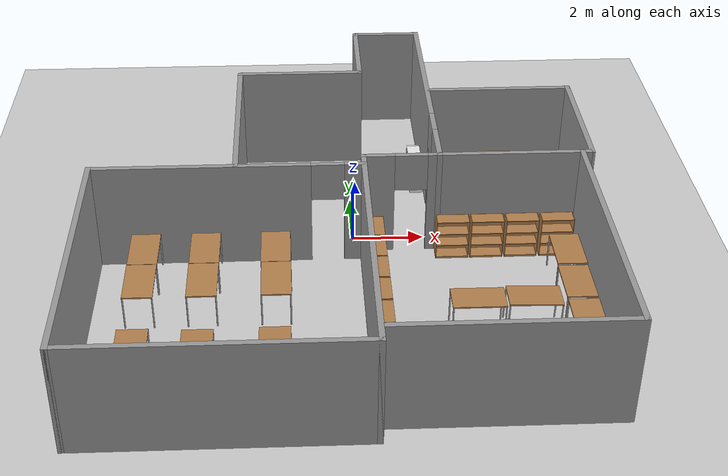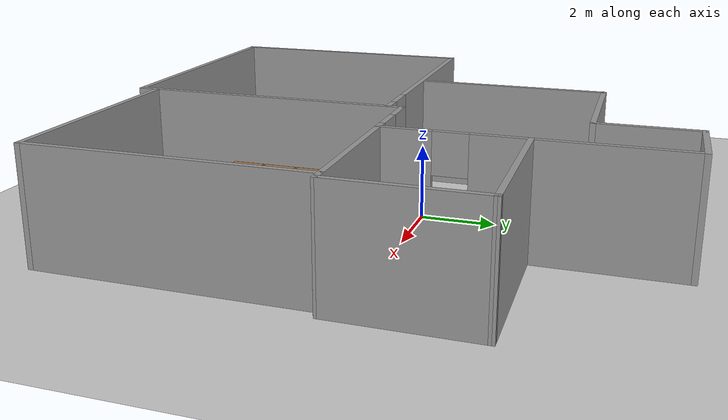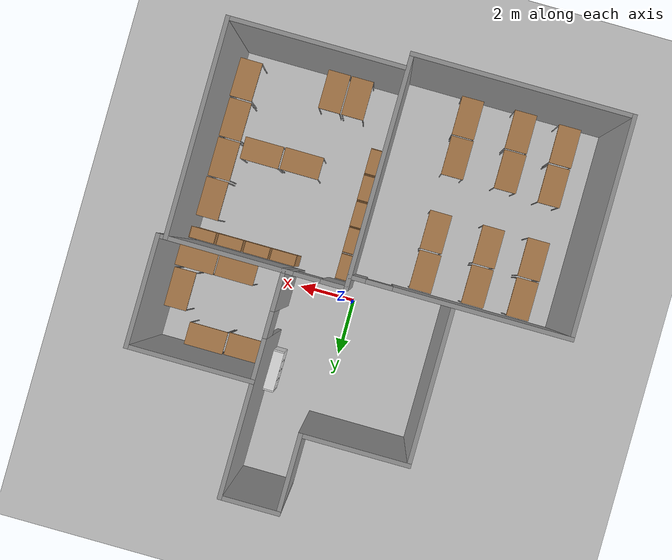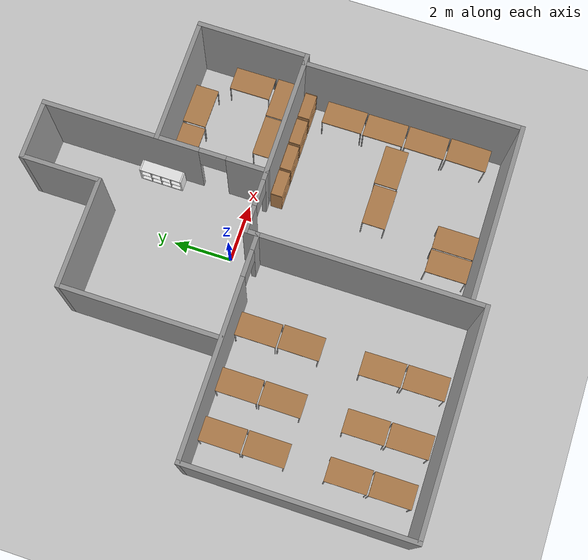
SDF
<sdf version="1.6">
 <world name="default">
  <model name="ground_plane">
   <static>1</static>
   <link name="link">
    <collision name="collision">
     <geometry><plane><normal>0 0 1</normal><size>100 100</size></plane></geometry>
     <surface><friction><ode><mu>100</mu><mu2>50</mu2></ode></friction></surface>
    </collision>
    <visual name="visual">
     <cast_shadows>0</cast_shadows>
     <geometry><plane><normal>0 0 1</normal><size>100 100</size></plane></geometry>
     <material>
      <script><uri>file://media/materials/scripts/gazebo.material</uri><name>Gazebo/Grey</name></script>
     </material>
    </visual>
   </link>
  </model>
  <gravity>0 0 -9.8</gravity>
  <magnetic_field>6e-06 2.3e-05 -4.2e-05</magnetic_field>
  <atmosphere type="adiabatic"/>
  <physics name="default_physics" default="0" type="ode">
   <max_step_size>0.001</max_step_size>
   <real_time_factor>1</real_time_factor>
   <real_time_update_rate>1000</real_time_update_rate>
  </physics>
  <scene><ambient>0.4 0.4 0.4 1</ambient><background>0.7 0.7 0.7 1</background><shadows>1</shadows></scene>
  <spherical_coordinates>
   <surface_model>EARTH_WGS84</surface_model>
   <latitude_deg>0</latitude_deg>
   <longitude_deg>0</longitude_deg>
   <elevation>0</elevation>
   <heading_deg>0</heading_deg>
  </spherical_coordinates>
  <model name="bh9f_lab">
   <pose>-0.31244 -0.65271 0 0 -0 0</pose>
   <link name="Wall_0">
    <pose>-3.1331 -0.253 0 0 -0 3.14159</pose>
    <visual name="Wall_0_Visual_0">
     <pose>-3.46145 0 1.55 0 -0 0</pose>
     <geometry><box><size>0.601096 0.15 3.1</size></box></geometry>
     <material>
      <script><uri>file://media/materials/scripts/gazebo.material</uri><name>Gazebo/Grey</name></script>
      <ambient>1 1 1 1</ambient>
     </material>
    </visual>
    <collision name="Wall_0_Collision_0">
     <geometry><box><size>0.601096 0.15 3.1</size></box></geometry>
     <pose>-3.46145 0 1.55 0 -0 0</pose>
    </collision>
    <visual name="Wall_0_Visual_1">
     <pose>0.750548 0 1.55 0 -0 0</pose>
     <geometry><box><size>6.0229 0.15 3.1</size></box></geometry>
     <material>
      <script><uri>file://media/materials/scripts/gazebo.material</uri><name>Gazebo/Grey</name></script>
      <ambient>1 1 1 1</ambient>
     </material>
    </visual>
    <collision name="Wall_0_Collision_1">
     <geometry><box><size>6.0229 0.15 3.1</size></box></geometry>
     <pose>0.750548 0 1.55 0 -0 0</pose>
    </collision>
    <visual name="Wall_0_Visual_3">
     <pose>-2.7109 0 2.55 0 -0 0</pose>
     <geometry><box><size>0.9 0.15 1.1</size></box></geometry>
     <material>
      <script><uri>file://media/materials/scripts/gazebo.material</uri><name>Gazebo/Grey</name></script>
      <ambient>1 1 1 1</ambient>
     </material>
    </visual>
    <collision name="Wall_0_Collision_3">
     <geometry><box><size>0.9 0.15 1.1</size></box></geometry>
     <pose>-2.7109 0 2.55 0 -0 0</pose>
    </collision>
   </link>
   <link name="Wall_12">
    <collision name="Wall_12_Collision">
     <geometry><box><size>7.44 0.15 3.1</size></box></geometry>
     <pose>0 0 1.55 0 -0 0</pose>
    </collision>
    <visual name="Wall_12_Visual">
     <pose>0 0 1.55 0 -0 0</pose>
     <geometry><box><size>7.44 0.15 3.1</size></box></geometry>
     <material>
      <script><uri>file://media/materials/scripts/gazebo.material</uri><name>Gazebo/Grey</name></script>
      <ambient>1 1 1 1</ambient>
     </material>
    </visual>
    <pose>6.5499 -3.516 0 0 0 -1.5708</pose>
   </link>
   <link name="Wall_14">
    <collision name="Wall_14_Collision">
     <geometry><box><size>6 0.15 3.1</size></box></geometry>
     <pose>0 0 1.55 0 -0 0</pose>
    </collision>
    <visual name="Wall_14_Visual">
     <pose>0 0 1.55 0 -0 0</pose>
     <geometry><box><size>6 0.15 3.1</size></box></geometry>
     <material>
      <script><uri>file://media/materials/scripts/gazebo.material</uri><name>Gazebo/Grey</name></script>
      <ambient>1 1 1 1</ambient>
     </material>
    </visual>
    <pose>3.6249 -7.161 0 0 -0 3.14159</pose>
   </link>
   <link name="Wall_16">
    <collision name="Wall_16_Collision">
     <geometry><box><size>3.83 0.15 3.1</size></box></geometry>
     <pose>0 0 1.55 0 -0 0</pose>
    </collision>
    <visual name="Wall_16_Visual">
     <pose>0 0 1.55 0 -0 0</pose>
     <geometry><box><size>3.83 0.15 3.1</size></box></geometry>
     <material>
      <script><uri>file://media/materials/scripts/gazebo.material</uri><name>Gazebo/Grey</name></script>
      <ambient>1 1 1 1</ambient>
     </material>
    </visual>
    <pose>6.8149 1.975 0 0 -0 1.56808</pose>
   </link>
   <link name="Wall_18">
    <collision name="Wall_18_Collision">
     <geometry><box><size>4.33 0.15 3.1</size></box></geometry>
     <pose>0 0 1.55 0 -0 0</pose>
    </collision>
    <visual name="Wall_18_Visual">
     <pose>0 0 1.55 0 -0 0</pose>
     <geometry><box><size>4.33 0.15 3.1</size></box></geometry>
     <material>
      <script><uri>file://media/materials/scripts/gazebo.material</uri><name>Gazebo/Grey</name></script>
      <ambient>1 1 1 1</ambient>
     </material>
    </visual>
    <pose>4.7299 3.815 0 0 -0 3.14159</pose>
   </link>
   <link name="Wall_2">
    <collision name="Wall_2_Collision">
     <geometry><box><size>7.542 0.15 3.1</size></box></geometry>
     <pose>0 0 1.55 0 -0 0</pose>
    </collision>
    <visual name="Wall_2_Visual">
     <pose>0 0 1.55 0 -0 0</pose>
     <geometry><box><size>7.542 0.15 3.1</size></box></geometry>
     <material>
      <script><uri>file://media/materials/scripts/gazebo.material</uri><name>Gazebo/Grey</name></script>
      <ambient>1 1 1 1</ambient>
     </material>
    </visual>
    <pose>-6.8201 -3.949 0 0 0 -1.5708</pose>
   </link>
   <link name="Wall_20">
    <pose>2.6379 3.89 0 0 -0 1.5708</pose>
    <visual name="Wall_20_Visual_0">
     <pose>-3.11825 0 1.55 0 -0 0</pose>
     <geometry><box><size>1.42351 0.15 3.1</size></box></geometry>
     <material>
      <script><uri>file://media/materials/scripts/gazebo.material</uri><name>Gazebo/Grey</name></script>
      <ambient>1 1 1 1</ambient>
     </material>
    </visual>
    <collision name="Wall_20_Collision_0">
     <geometry><box><size>1.42351 0.15 3.1</size></box></geometry>
     <pose>-3.11825 0 1.55 0 -0 0</pose>
    </collision>
    <visual name="Wall_20_Visual_1">
     <pose>1.16175 0 1.55 0 -0 0</pose>
     <geometry><box><size>5.33649 0.15 3.1</size></box></geometry>
     <material>
      <script><uri>file://media/materials/scripts/gazebo.material</uri><name>Gazebo/Grey</name></script>
      <ambient>1 1 1 1</ambient>
     </material>
    </visual>
    <collision name="Wall_20_Collision_1">
     <geometry><box><size>5.33649 0.15 3.1</size></box></geometry>
     <pose>1.16175 0 1.55 0 -0 0</pose>
    </collision>
    <visual name="Wall_20_Visual_3">
     <pose>-1.95649 0 2.55 0 -0 0</pose>
     <geometry><box><size>0.9 0.15 1.1</size></box></geometry>
     <material>
      <script><uri>file://media/materials/scripts/gazebo.material</uri><name>Gazebo/Grey</name></script>
      <ambient>1 1 1 1</ambient>
     </material>
    </visual>
    <collision name="Wall_20_Collision_3">
     <geometry><box><size>0.9 0.15 1.1</size></box></geometry>
     <pose>-1.95649 0 2.55 0 -0 0</pose>
    </collision>
   </link>
   <link name="Wall_24">
    <collision name="Wall_24_Collision">
     <geometry><box><size>2.089 0.15 3.1</size></box></geometry>
     <pose>0 0 1.55 0 -0 0</pose>
    </collision>
    <visual name="Wall_24_Visual">
     <pose>0 0 1.55 0 -0 0</pose>
     <geometry><box><size>2.089 0.15 3.1</size></box></geometry>
     <material>
      <script><uri>file://media/materials/scripts/gazebo.material</uri><name>Gazebo/Grey</name></script>
      <ambient>1 1 1 1</ambient>
     </material>
    </visual>
    <pose>1.6684 7.645 0 0 -0 3.14159</pose>
   </link>
   <link name="Wall_26">
    <collision name="Wall_26_Collision">
     <geometry><box><size>2.75 0.15 3.1</size></box></geometry>
     <pose>0 0 1.55 0 -0 0</pose>
    </collision>
    <visual name="Wall_26_Visual">
     <pose>0 0 1.55 0 -0 0</pose>
     <geometry><box><size>2.75 0.15 3.1</size></box></geometry>
     <material>
      <script><uri>file://media/materials/scripts/gazebo.material</uri><name>Gazebo/Grey</name></script>
      <ambient>1 1 1 1</ambient>
     </material>
    </visual>
    <pose>0.698898 6.345 0 0 0 -1.5708</pose>
   </link>
   <link name="Wall_28">
    <collision name="Wall_28_Collision">
     <geometry><box><size>3.75 0.15 3.1</size></box></geometry>
     <pose>0 0 1.55 0 -0 0</pose>
    </collision>
    <visual name="Wall_28_Visual">
     <pose>0 0 1.55 0 -0 0</pose>
     <geometry><box><size>3.75 0.15 3.1</size></box></geometry>
     <material>
      <script><uri>file://media/materials/scripts/gazebo.material</uri><name>Gazebo/Grey</name></script>
      <ambient>1 1 1 1</ambient>
     </material>
    </visual>
    <pose>-1.1011 5.045 0 0 -0 3.14159</pose>
   </link>
   <link name="Wall_30">
    <collision name="Wall_30_Collision">
     <geometry><box><size>5.41 0.15 3.1</size></box></geometry>
     <pose>0 0 1.55 0 -0 0</pose>
    </collision>
    <visual name="Wall_30_Visual">
     <pose>0 0 1.55 0 -0 0</pose>
     <geometry><box><size>5.41 0.15 3.1</size></box></geometry>
     <material>
      <script><uri>file://media/materials/scripts/gazebo.material</uri><name>Gazebo/Grey</name></script>
      <ambient>1 1 1 1</ambient>
     </material>
    </visual>
    <pose>-2.9011 2.415 0 0 0 -1.5708</pose>
   </link>
   <link name="Wall_4">
    <collision name="Wall_4_Collision">
     <geometry><box><size>7.53 0.15 3.1</size></box></geometry>
     <pose>0 0 1.55 0 -0 0</pose>
    </collision>
    <visual name="Wall_4_Visual">
     <pose>0 0 1.55 0 -0 0</pose>
     <geometry><box><size>7.53 0.15 3.1</size></box></geometry>
     <material>
      <script><uri>file://media/materials/scripts/gazebo.material</uri><name>Gazebo/Grey</name></script>
      <ambient>1 1 1 1</ambient>
     </material>
    </visual>
    <pose>-3.1301 -7.645 0 0 -0 0</pose>
   </link>
   <link name="Wall_6">
    <collision name="Wall_6_Collision">
     <geometry><box><size>7.93 0.15 3.1</size></box></geometry>
     <pose>0 0 1.55 0 -0 0</pose>
    </collision>
    <visual name="Wall_6_Visual">
     <pose>0 0 1.55 0 -0 0</pose>
     <geometry><box><size>7.93 0.15 3.1</size></box></geometry>
     <material>
      <script><uri>file://media/materials/scripts/gazebo.material</uri><name>Gazebo/Grey</name></script>
      <ambient>1 1 1 1</ambient>
     </material>
    </visual>
    <pose>0.559898 -3.755 0 0 -0 1.5708</pose>
   </link>
   <link name="Wall_8">
    <pose>3.6849 0.135 0 0 -0 0</pose>
    <visual name="Wall_8_Visual_0">
     <pose>-2.73161 0 1.55 0 -0 0</pose>
     <geometry><box><size>0.936778 0.15 3.1</size></box></geometry>
     <material>
      <script><uri>file://media/materials/scripts/gazebo.material</uri><name>Gazebo/Grey</name></script>
      <ambient>1 1 1 1</ambient>
     </material>
    </visual>
    <collision name="Wall_8_Collision_0">
     <geometry><box><size>0.936778 0.15 3.1</size></box></geometry>
     <pose>-2.73161 0 1.55 0 -0 0</pose>
    </collision>
    <visual name="Wall_8_Visual_1">
     <pose>0.918389 0 1.55 0 -0 0</pose>
     <geometry><box><size>4.56322 0.15 3.1</size></box></geometry>
     <material>
      <script><uri>file://media/materials/scripts/gazebo.material</uri><name>Gazebo/Grey</name></script>
      <ambient>1 1 1 1</ambient>
     </material>
    </visual>
    <collision name="Wall_8_Collision_1">
     <geometry><box><size>4.56322 0.15 3.1</size></box></geometry>
     <pose>0.918389 0 1.55 0 -0 0</pose>
    </collision>
    <visual name="Wall_8_Visual_3">
     <pose>-1.81322 0 2.55 0 -0 0</pose>
     <geometry><box><size>0.9 0.15 1.1</size></box></geometry>
     <material>
      <script><uri>file://media/materials/scripts/gazebo.material</uri><name>Gazebo/Grey</name></script>
      <ambient>1 1 1 1</ambient>
     </material>
    </visual>
    <collision name="Wall_8_Collision_3">
     <geometry><box><size>0.9 0.15 1.1</size></box></geometry>
     <pose>-1.81322 0 2.55 0 -0 0</pose>
    </collision>
   </link>
   <static>1</static>
  </model>
  <light name="user_directional_light_0" type="directional">
   <pose>0.149762 -0.768978 1 0 -0 0</pose>
   <diffuse>0.5 0.5 0.5 1</diffuse>
   <specular>0.1 0.1 0.1 1</specular>
   <direction>0.1 0.1 -0.9</direction>
   <attenuation>
    <range>20</range>
    <constant>0.5</constant>
    <linear>0.01</linear>
    <quadratic>0.001</quadratic>
   </attenuation>
  </light>
  <light name="user_directional_light_1" type="directional">
   <pose>0.177428 -0.848328 1 0 -0 0</pose>
   <diffuse>0.5 0.5 0.5 1</diffuse>
   <specular>0.1 0.1 0.1 1</specular>
   <direction>0.1 0.1 -0.9</direction>
   <attenuation>
    <range>20</range>
    <constant>0.5</constant>
    <linear>0.01</linear>
    <quadratic>0.001</quadratic>
   </attenuation>
  </light>
  <model name="bookcase">
   <link name="dummy_link">
    <inertial>
     <pose>0 0 0.335152 0 -0 0</pose>
     <mass>33</mass>
     <inertia>
      <ixx>7.54617</ixx>
      <ixy>0</ixy>
      <ixz>0</ixz>
      <iyy>2.12412</iyy>
      <iyz>1.60768e-16</iyz>
      <izz>5.42205</izz>
     </inertia>
    </inertial>
    <collision name="dummy_link_fixed_joint_lump__bookcase_bottom_link_collision_1">
     <pose>0 0 0.025 0 -0 0</pose>
     <geometry><box><size>0.39 1.39 0.05</size></box></geometry>
    </collision>
    <collision name="dummy_link_fixed_joint_lump__separation_4_link_collision_2">
     <pose>0 -0.345 0.21875 0 -0 0</pose>
     <geometry><box><size>0.39 0.015 0.33</size></box></geometry>
    </collision>
    <collision name="dummy_link_fixed_joint_lump__separation_5_link_collision_3">
     <pose>0 0 0.21875 0 -0 0</pose>
     <geometry><box><size>0.39 0.015 0.33</size></box></geometry>
    </collision>
    <collision name="dummy_link_fixed_joint_lump__separation_6_link_collision_4">
     <pose>0 0.345 0.21875 0 -0 0</pose>
     <geometry><box><size>0.39 0.015 0.33</size></box></geometry>
    </collision>
    <collision name="dummy_link_fixed_joint_lump__bookcase_left_collision_5">
     <pose>0 -0.72 0.395 0 -0 0</pose>
     <geometry><box><size>0.39 0.05 0.79</size></box></geometry>
    </collision>
    <collision name="dummy_link_fixed_joint_lump__bookcase_middle_collision_6">
     <pose>0 0 0.395 0 -0 0</pose>
     <geometry><box><size>0.39 1.39 0.015</size></box></geometry>
    </collision>
    <collision name="dummy_link_fixed_joint_lump__bookcase_right_collision_7">
     <pose>0 0.72 0.395 0 -0 0</pose>
     <geometry><box><size>0.39 0.05 0.79</size></box></geometry>
    </collision>
    <collision name="dummy_link_fixed_joint_lump__bookcase_top_link_collision_8">
     <pose>0 0 0.765 0 -0 0</pose>
     <geometry><box><size>0.39 1.39 0.05</size></box></geometry>
    </collision>
    <collision name="dummy_link_fixed_joint_lump__separation_1_link_collision_9">
     <pose>0 -0.345 0.57125 0 -0 0</pose>
     <geometry><box><size>0.39 0.015 0.33</size></box></geometry>
    </collision>
    <collision name="dummy_link_fixed_joint_lump__separation_2_link_collision_10">
     <pose>0 0 0.57125 0 -0 0</pose>
     <geometry><box><size>0.39 0.015 0.33</size></box></geometry>
    </collision>
    <collision name="dummy_link_fixed_joint_lump__separation_3_link_collision_11">
     <pose>0 0.345 0.57125 0 -0 0</pose>
     <geometry><box><size>0.39 0.015 0.33</size></box></geometry>
    </collision>
    <visual name="dummy_link_fixed_joint_lump__bookcase_bottom_link_visual_1">
     <pose>0 0 0.025 0 -0 0</pose>
     <geometry><box><size>0.39 1.39 0.05</size></box></geometry>
     <material>
      <script><name>Gazebo/White</name><uri>file://media/materials/scripts/gazebo.material</uri></script>
     </material>
    </visual>
    <visual name="dummy_link_fixed_joint_lump__separation_4_link_visual_2">
     <pose>0 -0.345 0.21875 0 -0 0</pose>
     <geometry><box><size>0.39 0.015 0.3375</size></box></geometry>
    </visual>
    <visual name="dummy_link_fixed_joint_lump__separation_5_link_visual_3">
     <pose>0 0 0.21875 0 -0 0</pose>
     <geometry><box><size>0.39 0.015 0.3375</size></box></geometry>
    </visual>
    <visual name="dummy_link_fixed_joint_lump__separation_6_link_visual_4">
     <pose>0 0.345 0.21875 0 -0 0</pose>
     <geometry><box><size>0.39 0.015 0.3375</size></box></geometry>
    </visual>
    <visual name="dummy_link_fixed_joint_lump__bookcase_left_visual_5">
     <pose>0 -0.72 0.395 0 -0 0</pose>
     <geometry><box><size>0.39 0.05 0.79</size></box></geometry>
     <material>
      <script><name>Gazebo/White</name><uri>file://media/materials/scripts/gazebo.material</uri></script>
     </material>
    </visual>
    <visual name="dummy_link_fixed_joint_lump__bookcase_middle_visual_6">
     <pose>0 0 0.395 0 -0 0</pose>
     <geometry><box><size>0.39 1.39 0.015</size></box></geometry>
     <material>
      <script><name>Gazebo/White</name><uri>file://media/materials/scripts/gazebo.material</uri></script>
     </material>
    </visual>
    <visual name="dummy_link_fixed_joint_lump__bookcase_right_visual_7">
     <pose>0 0.72 0.395 0 -0 0</pose>
     <geometry><box><size>0.39 0.05 0.79</size></box></geometry>
     <material>
      <script><name>Gazebo/White</name><uri>file://media/materials/scripts/gazebo.material</uri></script>
     </material>
    </visual>
    <visual name="dummy_link_fixed_joint_lump__bookcase_top_link_visual_8">
     <pose>0 0 0.765 0 -0 0</pose>
     <geometry><box><size>0.39 1.39 0.05</size></box></geometry>
     <material>
      <script><name>Gazebo/White</name><uri>file://media/materials/scripts/gazebo.material</uri></script>
     </material>
    </visual>
    <visual name="dummy_link_fixed_joint_lump__separation_1_link_visual_9">
     <pose>0 -0.345 0.57125 0 -0 0</pose>
     <geometry><box><size>0.39 0.015 0.3375</size></box></geometry>
    </visual>
    <visual name="dummy_link_fixed_joint_lump__separation_2_link_visual_10">
     <pose>0 0 0.57125 0 -0 0</pose>
     <geometry><box><size>0.39 0.015 0.3375</size></box></geometry>
    </visual>
    <visual name="dummy_link_fixed_joint_lump__separation_3_link_visual_11">
     <pose>0 0.345 0.57125 0 -0 0</pose>
     <geometry><box><size>0.39 0.015 0.3375</size></box></geometry>
    </visual>
   </link>
   <pose>2.03555 3.11584 -4e-06 -4e-06 -6e-06 -0.005442</pose>
  </model>
  <model name="table">
   <static>0</static>
   <link name="link">
    <collision name="surface">
     <pose>0 0 1 0 -0 0</pose>
     <geometry><box><size>1.5 0.8 0.03</size></box></geometry>
     <surface><friction><ode><mu>0.6</mu><mu2>0.6</mu2></ode></friction></surface>
    </collision>
    <visual name="visual1">
     <pose>0 0 1 0 -0 0</pose>
     <geometry><box><size>1.4 0.8 0.04</size></box></geometry>
     <material>
      <script><uri>file://media/materials/scripts/gazebo.material</uri><name>Gazebo/Wood</name></script>
     </material>
    </visual>
    <collision name="front_left_leg">
     <pose>0.68 0.38 0.5 0 -0 0</pose>
     <geometry><cylinder><radius>0.02</radius><length>1</length></cylinder></geometry>
    </collision>
    <visual name="front_left_leg">
     <pose>0.68 0.38 0.5 0 -0 0</pose>
     <geometry><cylinder><radius>0.02</radius><length>1</length></cylinder></geometry>
     <material>
      <script><uri>file://media/materials/scripts/gazebo.material</uri><name>Gazebo/Grey</name></script>
     </material>
    </visual>
    <collision name="front_right_leg">
     <pose>0.68 -0.38 0.5 0 -0 0</pose>
     <geometry><cylinder><radius>0.02</radius><length>1</length></cylinder></geometry>
    </collision>
    <visual name="front_right_leg">
     <pose>0.68 -0.38 0.5 0 -0 0</pose>
     <geometry><cylinder><radius>0.02</radius><length>1</length></cylinder></geometry>
     <material>
      <script><uri>file://media/materials/scripts/gazebo.material</uri><name>Gazebo/Grey</name></script>
     </material>
    </visual>
    <collision name="back_right_leg">
     <pose>-0.68 -0.38 0.5 0 -0 0</pose>
     <geometry><cylinder><radius>0.02</radius><length>1</length></cylinder></geometry>
    </collision>
    <visual name="back_right_leg">
     <pose>-0.68 -0.38 0.5 0 -0 0</pose>
     <geometry><cylinder><radius>0.02</radius><length>1</length></cylinder></geometry>
     <material>
      <script><uri>file://media/materials/scripts/gazebo.material</uri><name>Gazebo/Grey</name></script>
     </material>
    </visual>
    <collision name="back_left_leg">
     <pose>-0.68 0.38 0.5 0 -0 0</pose>
     <geometry><cylinder><radius>0.02</radius><length>1</length></cylinder></geometry>
    </collision>
    <visual name="back_left_leg">
     <pose>-0.68 0.38 0.5 0 -0 0</pose>
     <geometry><cylinder><radius>0.02</radius><length>1</length></cylinder></geometry>
     <material>
      <script><uri>file://media/materials/scripts/gazebo.material</uri><name>Gazebo/Grey</name></script>
     </material>
    </visual>
    <inertial>
     <inertia><ixx>1</ixx><ixy>0</ixy><ixz>0</ixz><iyy>1</iyy><iyz>0</iyz><izz>1</izz></inertia>
     <mass>1</mass>
    </inertial>
   </link>
   <pose>4.57969 2.60173 0.015107 5e-06 0.02158 -5e-06</pose>
  </model>
  <model name="table_clone">
   <static>0</static>
   <link name="link">
    <collision name="surface">
     <pose>0 0 1 0 -0 0</pose>
     <geometry><box><size>1.5 0.8 0.03</size></box></geometry>
     <surface><friction><ode><mu>0.6</mu><mu2>0.6</mu2></ode></friction></surface>
    </collision>
    <visual name="visual1">
     <pose>0 0 1 0 -0 0</pose>
     <geometry><box><size>1.4 0.8 0.04</size></box></geometry>
     <material>
      <script><uri>file://media/materials/scripts/gazebo.material</uri><name>Gazebo/Wood</name></script>
     </material>
    </visual>
    <collision name="front_left_leg">
     <pose>0.68 0.38 0.5 0 -0 0</pose>
     <geometry><cylinder><radius>0.02</radius><length>1</length></cylinder></geometry>
    </collision>
    <visual name="front_left_leg">
     <pose>0.68 0.38 0.5 0 -0 0</pose>
     <geometry><cylinder><radius>0.02</radius><length>1</length></cylinder></geometry>
     <material>
      <script><uri>file://media/materials/scripts/gazebo.material</uri><name>Gazebo/Grey</name></script>
     </material>
    </visual>
    <collision name="front_right_leg">
     <pose>0.68 -0.38 0.5 0 -0 0</pose>
     <geometry><cylinder><radius>0.02</radius><length>1</length></cylinder></geometry>
    </collision>
    <visual name="front_right_leg">
     <pose>0.68 -0.38 0.5 0 -0 0</pose>
     <geometry><cylinder><radius>0.02</radius><length>1</length></cylinder></geometry>
     <material>
      <script><uri>file://media/materials/scripts/gazebo.material</uri><name>Gazebo/Grey</name></script>
     </material>
    </visual>
    <collision name="back_right_leg">
     <pose>-0.68 -0.38 0.5 0 -0 0</pose>
     <geometry><cylinder><radius>0.02</radius><length>1</length></cylinder></geometry>
    </collision>
    <visual name="back_right_leg">
     <pose>-0.68 -0.38 0.5 0 -0 0</pose>
     <geometry><cylinder><radius>0.02</radius><length>1</length></cylinder></geometry>
     <material>
      <script><uri>file://media/materials/scripts/gazebo.material</uri><name>Gazebo/Grey</name></script>
     </material>
    </visual>
    <collision name="back_left_leg">
     <pose>-0.68 0.38 0.5 0 -0 0</pose>
     <geometry><cylinder><radius>0.02</radius><length>1</length></cylinder></geometry>
    </collision>
    <visual name="back_left_leg">
     <pose>-0.68 0.38 0.5 0 -0 0</pose>
     <geometry><cylinder><radius>0.02</radius><length>1</length></cylinder></geometry>
     <material>
      <script><uri>file://media/materials/scripts/gazebo.material</uri><name>Gazebo/Grey</name></script>
     </material>
    </visual>
    <inertial>
     <inertia><ixx>1</ixx><ixy>0</ixy><ixz>0</ixz><iyy>1</iyy><iyz>0</iyz><izz>1</izz></inertia>
     <mass>1</mass>
    </inertial>
   </link>
   <pose>3.15046 2.58517 -3e-06 -1e-06 -4e-06 5e-06</pose>
  </model>
  <model name="table_clone_0">
   <static>0</static>
   <link name="link">
    <collision name="surface">
     <pose>0 0 1 0 -0 0</pose>
     <geometry><box><size>1.5 0.8 0.03</size></box></geometry>
     <surface><friction><ode><mu>0.6</mu><mu2>0.6</mu2></ode></friction></surface>
    </collision>
    <visual name="visual1">
     <pose>0 0 1 0 -0 0</pose>
     <geometry><box><size>1.4 0.8 0.04</size></box></geometry>
     <material>
      <script><uri>file://media/materials/scripts/gazebo.material</uri><name>Gazebo/Wood</name></script>
     </material>
    </visual>
    <collision name="front_left_leg">
     <pose>0.68 0.38 0.5 0 -0 0</pose>
     <geometry><cylinder><radius>0.02</radius><length>1</length></cylinder></geometry>
    </collision>
    <visual name="front_left_leg">
     <pose>0.68 0.38 0.5 0 -0 0</pose>
     <geometry><cylinder><radius>0.02</radius><length>1</length></cylinder></geometry>
     <material>
      <script><uri>file://media/materials/scripts/gazebo.material</uri><name>Gazebo/Grey</name></script>
     </material>
    </visual>
    <collision name="front_right_leg">
     <pose>0.68 -0.38 0.5 0 -0 0</pose>
     <geometry><cylinder><radius>0.02</radius><length>1</length></cylinder></geometry>
    </collision>
    <visual name="front_right_leg">
     <pose>0.68 -0.38 0.5 0 -0 0</pose>
     <geometry><cylinder><radius>0.02</radius><length>1</length></cylinder></geometry>
     <material>
      <script><uri>file://media/materials/scripts/gazebo.material</uri><name>Gazebo/Grey</name></script>
     </material>
    </visual>
    <collision name="back_right_leg">
     <pose>-0.68 -0.38 0.5 0 -0 0</pose>
     <geometry><cylinder><radius>0.02</radius><length>1</length></cylinder></geometry>
    </collision>
    <visual name="back_right_leg">
     <pose>-0.68 -0.38 0.5 0 -0 0</pose>
     <geometry><cylinder><radius>0.02</radius><length>1</length></cylinder></geometry>
     <material>
      <script><uri>file://media/materials/scripts/gazebo.material</uri><name>Gazebo/Grey</name></script>
     </material>
    </visual>
    <collision name="back_left_leg">
     <pose>-0.68 0.38 0.5 0 -0 0</pose>
     <geometry><cylinder><radius>0.02</radius><length>1</length></cylinder></geometry>
    </collision>
    <visual name="back_left_leg">
     <pose>-0.68 0.38 0.5 0 -0 0</pose>
     <geometry><cylinder><radius>0.02</radius><length>1</length></cylinder></geometry>
     <material>
      <script><uri>file://media/materials/scripts/gazebo.material</uri><name>Gazebo/Grey</name></script>
     </material>
    </visual>
    <inertial>
     <inertia><ixx>1</ixx><ixy>0</ixy><ixz>0</ixz><iyy>1</iyy><iyz>0</iyz><izz>1</izz></inertia>
     <mass>1</mass>
    </inertial>
   </link>
   <pose>5.67387 0.001172 -2.7e-05 -1e-06 -3e-06 -0.002717</pose>
  </model>
  <model name="table_clone_1">
   <static>0</static>
   <link name="link">
    <collision name="surface">
     <pose>0 0 1 0 -0 0</pose>
     <geometry><box><size>1.5 0.8 0.03</size></box></geometry>
     <surface><friction><ode><mu>0.6</mu><mu2>0.6</mu2></ode></friction></surface>
    </collision>
    <visual name="visual1">
     <pose>0 0 1 0 -0 0</pose>
     <geometry><box><size>1.4 0.8 0.04</size></box></geometry>
     <material>
      <script><uri>file://media/materials/scripts/gazebo.material</uri><name>Gazebo/Wood</name></script>
     </material>
    </visual>
    <collision name="front_left_leg">
     <pose>0.68 0.38 0.5 0 -0 0</pose>
     <geometry><cylinder><radius>0.02</radius><length>1</length></cylinder></geometry>
    </collision>
    <visual name="front_left_leg">
     <pose>0.68 0.38 0.5 0 -0 0</pose>
     <geometry><cylinder><radius>0.02</radius><length>1</length></cylinder></geometry>
     <material>
      <script><uri>file://media/materials/scripts/gazebo.material</uri><name>Gazebo/Grey</name></script>
     </material>
    </visual>
    <collision name="front_right_leg">
     <pose>0.68 -0.38 0.5 0 -0 0</pose>
     <geometry><cylinder><radius>0.02</radius><length>1</length></cylinder></geometry>
    </collision>
    <visual name="front_right_leg">
     <pose>0.68 -0.38 0.5 0 -0 0</pose>
     <geometry><cylinder><radius>0.02</radius><length>1</length></cylinder></geometry>
     <material>
      <script><uri>file://media/materials/scripts/gazebo.material</uri><name>Gazebo/Grey</name></script>
     </material>
    </visual>
    <collision name="back_right_leg">
     <pose>-0.68 -0.38 0.5 0 -0 0</pose>
     <geometry><cylinder><radius>0.02</radius><length>1</length></cylinder></geometry>
    </collision>
    <visual name="back_right_leg">
     <pose>-0.68 -0.38 0.5 0 -0 0</pose>
     <geometry><cylinder><radius>0.02</radius><length>1</length></cylinder></geometry>
     <material>
      <script><uri>file://media/materials/scripts/gazebo.material</uri><name>Gazebo/Grey</name></script>
     </material>
    </visual>
    <collision name="back_left_leg">
     <pose>-0.68 0.38 0.5 0 -0 0</pose>
     <geometry><cylinder><radius>0.02</radius><length>1</length></cylinder></geometry>
    </collision>
    <visual name="back_left_leg">
     <pose>-0.68 0.38 0.5 0 -0 0</pose>
     <geometry><cylinder><radius>0.02</radius><length>1</length></cylinder></geometry>
     <material>
      <script><uri>file://media/materials/scripts/gazebo.material</uri><name>Gazebo/Grey</name></script>
     </material>
    </visual>
    <inertial>
     <inertia><ixx>1</ixx><ixy>0</ixy><ixz>0</ixz><iyy>1</iyy><iyz>0</iyz><izz>1</izz></inertia>
     <mass>1</mass>
    </inertial>
   </link>
   <pose>4.2446 -0.006714 0.015089 -1e-06 -0.021568 -0.002717</pose>
  </model>
  <model name="table_clone_2">
   <static>0</static>
   <link name="link">
    <collision name="surface">
     <pose>0 0 1 0 -0 0</pose>
     <geometry><box><size>1.5 0.8 0.03</size></box></geometry>
     <surface><friction><ode><mu>0.6</mu><mu2>0.6</mu2></ode></friction></surface>
    </collision>
    <visual name="visual1">
     <pose>0 0 1 0 -0 0</pose>
     <geometry><box><size>1.4 0.8 0.04</size></box></geometry>
     <material>
      <script><uri>file://media/materials/scripts/gazebo.material</uri><name>Gazebo/Wood</name></script>
     </material>
    </visual>
    <collision name="front_left_leg">
     <pose>0.68 0.38 0.5 0 -0 0</pose>
     <geometry><cylinder><radius>0.02</radius><length>1</length></cylinder></geometry>
    </collision>
    <visual name="front_left_leg">
     <pose>0.68 0.38 0.5 0 -0 0</pose>
     <geometry><cylinder><radius>0.02</radius><length>1</length></cylinder></geometry>
     <material>
      <script><uri>file://media/materials/scripts/gazebo.material</uri><name>Gazebo/Grey</name></script>
     </material>
    </visual>
    <collision name="front_right_leg">
     <pose>0.68 -0.38 0.5 0 -0 0</pose>
     <geometry><cylinder><radius>0.02</radius><length>1</length></cylinder></geometry>
    </collision>
    <visual name="front_right_leg">
     <pose>0.68 -0.38 0.5 0 -0 0</pose>
     <geometry><cylinder><radius>0.02</radius><length>1</length></cylinder></geometry>
     <material>
      <script><uri>file://media/materials/scripts/gazebo.material</uri><name>Gazebo/Grey</name></script>
     </material>
    </visual>
    <collision name="back_right_leg">
     <pose>-0.68 -0.38 0.5 0 -0 0</pose>
     <geometry><cylinder><radius>0.02</radius><length>1</length></cylinder></geometry>
    </collision>
    <visual name="back_right_leg">
     <pose>-0.68 -0.38 0.5 0 -0 0</pose>
     <geometry><cylinder><radius>0.02</radius><length>1</length></cylinder></geometry>
     <material>
      <script><uri>file://media/materials/scripts/gazebo.material</uri><name>Gazebo/Grey</name></script>
     </material>
    </visual>
    <collision name="back_left_leg">
     <pose>-0.68 0.38 0.5 0 -0 0</pose>
     <geometry><cylinder><radius>0.02</radius><length>1</length></cylinder></geometry>
    </collision>
    <visual name="back_left_leg">
     <pose>-0.68 0.38 0.5 0 -0 0</pose>
     <geometry><cylinder><radius>0.02</radius><length>1</length></cylinder></geometry>
     <material>
      <script><uri>file://media/materials/scripts/gazebo.material</uri><name>Gazebo/Grey</name></script>
     </material>
    </visual>
    <inertial>
     <inertia><ixx>1</ixx><ixy>0</ixy><ixz>0</ixz><iyy>1</iyy><iyz>0</iyz><izz>1</izz></inertia>
     <mass>1</mass>
    </inertial>
   </link>
   <pose>5.94644 1.1813 -3e-06 -0 -4e-06 -1.56858</pose>
  </model>
  <model name="table_0_clone_0_clone_clone">
   <static>0</static>
   <link name="link">
    <collision name="surface">
     <pose>0 0 1 0 -0 0</pose>
     <geometry><box><size>1.5 0.8 0.03</size></box></geometry>
     <surface><friction><ode><mu>0.6</mu><mu2>0.6</mu2></ode></friction></surface>
    </collision>
    <visual name="visual1">
     <pose>0 0 1 0 -0 0</pose>
     <geometry><box><size>1.4 0.8 0.04</size></box></geometry>
     <material>
      <script><uri>file://media/materials/scripts/gazebo.material</uri><name>Gazebo/Wood</name></script>
     </material>
    </visual>
    <collision name="front_left_leg">
     <pose>0.68 0.38 0.5 0 -0 0</pose>
     <geometry><cylinder><radius>0.02</radius><length>1</length></cylinder></geometry>
    </collision>
    <visual name="front_left_leg">
     <pose>0.68 0.38 0.5 0 -0 0</pose>
     <geometry><cylinder><radius>0.02</radius><length>1</length></cylinder></geometry>
     <material>
      <script><uri>file://media/materials/scripts/gazebo.material</uri><name>Gazebo/Grey</name></script>
     </material>
    </visual>
    <collision name="front_right_leg">
     <pose>0.68 -0.38 0.5 0 -0 0</pose>
     <geometry><cylinder><radius>0.02</radius><length>1</length></cylinder></geometry>
    </collision>
    <visual name="front_right_leg">
     <pose>0.68 -0.38 0.5 0 -0 0</pose>
     <geometry><cylinder><radius>0.02</radius><length>1</length></cylinder></geometry>
     <material>
      <script><uri>file://media/materials/scripts/gazebo.material</uri><name>Gazebo/Grey</name></script>
     </material>
    </visual>
    <collision name="back_right_leg">
     <pose>-0.68 -0.38 0.5 0 -0 0</pose>
     <geometry><cylinder><radius>0.02</radius><length>1</length></cylinder></geometry>
    </collision>
    <visual name="back_right_leg">
     <pose>-0.68 -0.38 0.5 0 -0 0</pose>
     <geometry><cylinder><radius>0.02</radius><length>1</length></cylinder></geometry>
     <material>
      <script><uri>file://media/materials/scripts/gazebo.material</uri><name>Gazebo/Grey</name></script>
     </material>
    </visual>
    <collision name="back_left_leg">
     <pose>-0.68 0.38 0.5 0 -0 0</pose>
     <geometry><cylinder><radius>0.02</radius><length>1</length></cylinder></geometry>
    </collision>
    <visual name="back_left_leg">
     <pose>-0.68 0.38 0.5 0 -0 0</pose>
     <geometry><cylinder><radius>0.02</radius><length>1</length></cylinder></geometry>
     <material>
      <script><uri>file://media/materials/scripts/gazebo.material</uri><name>Gazebo/Grey</name></script>
     </material>
    </visual>
    <inertial>
     <inertia><ixx>1</ixx><ixy>0</ixy><ixz>0</ixz><iyy>1</iyy><iyz>0</iyz><izz>1</izz></inertia>
     <mass>1</mass>
    </inertial>
   </link>
   <pose>5.70429 -5.08192 -2.3e-05 0 7e-06 -1.57798</pose>
  </model>
  <model name="table_0_clone_0_clone_clone_0">
   <static>0</static>
   <link name="link">
    <collision name="surface">
     <pose>0 0 1 0 -0 0</pose>
     <geometry><box><size>1.5 0.8 0.03</size></box></geometry>
     <surface><friction><ode><mu>0.6</mu><mu2>0.6</mu2></ode></friction></surface>
    </collision>
    <visual name="visual1">
     <pose>0 0 1 0 -0 0</pose>
     <geometry><box><size>1.4 0.8 0.04</size></box></geometry>
     <material>
      <script><uri>file://media/materials/scripts/gazebo.material</uri><name>Gazebo/Wood</name></script>
     </material>
    </visual>
    <collision name="front_left_leg">
     <pose>0.68 0.38 0.5 0 -0 0</pose>
     <geometry><cylinder><radius>0.02</radius><length>1</length></cylinder></geometry>
    </collision>
    <visual name="front_left_leg">
     <pose>0.68 0.38 0.5 0 -0 0</pose>
     <geometry><cylinder><radius>0.02</radius><length>1</length></cylinder></geometry>
     <material>
      <script><uri>file://media/materials/scripts/gazebo.material</uri><name>Gazebo/Grey</name></script>
     </material>
    </visual>
    <collision name="front_right_leg">
     <pose>0.68 -0.38 0.5 0 -0 0</pose>
     <geometry><cylinder><radius>0.02</radius><length>1</length></cylinder></geometry>
    </collision>
    <visual name="front_right_leg">
     <pose>0.68 -0.38 0.5 0 -0 0</pose>
     <geometry><cylinder><radius>0.02</radius><length>1</length></cylinder></geometry>
     <material>
      <script><uri>file://media/materials/scripts/gazebo.material</uri><name>Gazebo/Grey</name></script>
     </material>
    </visual>
    <collision name="back_right_leg">
     <pose>-0.68 -0.38 0.5 0 -0 0</pose>
     <geometry><cylinder><radius>0.02</radius><length>1</length></cylinder></geometry>
    </collision>
    <visual name="back_right_leg">
     <pose>-0.68 -0.38 0.5 0 -0 0</pose>
     <geometry><cylinder><radius>0.02</radius><length>1</length></cylinder></geometry>
     <material>
      <script><uri>file://media/materials/scripts/gazebo.material</uri><name>Gazebo/Grey</name></script>
     </material>
    </visual>
    <collision name="back_left_leg">
     <pose>-0.68 0.38 0.5 0 -0 0</pose>
     <geometry><cylinder><radius>0.02</radius><length>1</length></cylinder></geometry>
    </collision>
    <visual name="back_left_leg">
     <pose>-0.68 0.38 0.5 0 -0 0</pose>
     <geometry><cylinder><radius>0.02</radius><length>1</length></cylinder></geometry>
     <material>
      <script><uri>file://media/materials/scripts/gazebo.material</uri><name>Gazebo/Grey</name></script>
     </material>
    </visual>
    <inertial>
     <inertia><ixx>1</ixx><ixy>0</ixy><ixz>0</ixz><iyy>1</iyy><iyz>0</iyz><izz>1</izz></inertia>
     <mass>1</mass>
    </inertial>
   </link>
   <pose>5.71044 -6.51123 0.0151 -2e-06 0.021572 -1.57798</pose>
  </model>
  <model name="table_0_clone_0_clone_clone_1">
   <static>0</static>
   <link name="link">
    <collision name="surface">
     <pose>0 0 1 0 -0 0</pose>
     <geometry><box><size>1.5 0.8 0.03</size></box></geometry>
     <surface><friction><ode><mu>0.6</mu><mu2>0.6</mu2></ode></friction></surface>
    </collision>
    <visual name="visual1">
     <pose>0 0 1 0 -0 0</pose>
     <geometry><box><size>1.4 0.8 0.04</size></box></geometry>
     <material>
      <script><uri>file://media/materials/scripts/gazebo.material</uri><name>Gazebo/Wood</name></script>
     </material>
    </visual>
    <collision name="front_left_leg">
     <pose>0.68 0.38 0.5 0 -0 0</pose>
     <geometry><cylinder><radius>0.02</radius><length>1</length></cylinder></geometry>
    </collision>
    <visual name="front_left_leg">
     <pose>0.68 0.38 0.5 0 -0 0</pose>
     <geometry><cylinder><radius>0.02</radius><length>1</length></cylinder></geometry>
     <material>
      <script><uri>file://media/materials/scripts/gazebo.material</uri><name>Gazebo/Grey</name></script>
     </material>
    </visual>
    <collision name="front_right_leg">
     <pose>0.68 -0.38 0.5 0 -0 0</pose>
     <geometry><cylinder><radius>0.02</radius><length>1</length></cylinder></geometry>
    </collision>
    <visual name="front_right_leg">
     <pose>0.68 -0.38 0.5 0 -0 0</pose>
     <geometry><cylinder><radius>0.02</radius><length>1</length></cylinder></geometry>
     <material>
      <script><uri>file://media/materials/scripts/gazebo.material</uri><name>Gazebo/Grey</name></script>
     </material>
    </visual>
    <collision name="back_right_leg">
     <pose>-0.68 -0.38 0.5 0 -0 0</pose>
     <geometry><cylinder><radius>0.02</radius><length>1</length></cylinder></geometry>
    </collision>
    <visual name="back_right_leg">
     <pose>-0.68 -0.38 0.5 0 -0 0</pose>
     <geometry><cylinder><radius>0.02</radius><length>1</length></cylinder></geometry>
     <material>
      <script><uri>file://media/materials/scripts/gazebo.material</uri><name>Gazebo/Grey</name></script>
     </material>
    </visual>
    <collision name="back_left_leg">
     <pose>-0.68 0.38 0.5 0 -0 0</pose>
     <geometry><cylinder><radius>0.02</radius><length>1</length></cylinder></geometry>
    </collision>
    <visual name="back_left_leg">
     <pose>-0.68 0.38 0.5 0 -0 0</pose>
     <geometry><cylinder><radius>0.02</radius><length>1</length></cylinder></geometry>
     <material>
      <script><uri>file://media/materials/scripts/gazebo.material</uri><name>Gazebo/Grey</name></script>
     </material>
    </visual>
    <inertial>
     <inertia><ixx>1</ixx><ixy>0</ixy><ixz>0</ixz><iyy>1</iyy><iyz>0</iyz><izz>1</izz></inertia>
     <mass>1</mass>
    </inertial>
   </link>
   <pose>2.60823 -6.96246 -3e-06 0 -4e-06 -1.57084</pose>
  </model>
  <model name="table_0_clone_0_clone_clone_2">
   <static>0</static>
   <link name="link">
    <collision name="surface">
     <pose>0 0 1 0 -0 0</pose>
     <geometry><box><size>1.5 0.8 0.03</size></box></geometry>
     <surface><friction><ode><mu>0.6</mu><mu2>0.6</mu2></ode></friction></surface>
    </collision>
    <visual name="visual1">
     <pose>0 0 1 0 -0 0</pose>
     <geometry><box><size>1.4 0.8 0.04</size></box></geometry>
     <material>
      <script><uri>file://media/materials/scripts/gazebo.material</uri><name>Gazebo/Wood</name></script>
     </material>
    </visual>
    <collision name="front_left_leg">
     <pose>0.68 0.38 0.5 0 -0 0</pose>
     <geometry><cylinder><radius>0.02</radius><length>1</length></cylinder></geometry>
    </collision>
    <visual name="front_left_leg">
     <pose>0.68 0.38 0.5 0 -0 0</pose>
     <geometry><cylinder><radius>0.02</radius><length>1</length></cylinder></geometry>
     <material>
      <script><uri>file://media/materials/scripts/gazebo.material</uri><name>Gazebo/Grey</name></script>
     </material>
    </visual>
    <collision name="front_right_leg">
     <pose>0.68 -0.38 0.5 0 -0 0</pose>
     <geometry><cylinder><radius>0.02</radius><length>1</length></cylinder></geometry>
    </collision>
    <visual name="front_right_leg">
     <pose>0.68 -0.38 0.5 0 -0 0</pose>
     <geometry><cylinder><radius>0.02</radius><length>1</length></cylinder></geometry>
     <material>
      <script><uri>file://media/materials/scripts/gazebo.material</uri><name>Gazebo/Grey</name></script>
     </material>
    </visual>
    <collision name="back_right_leg">
     <pose>-0.68 -0.38 0.5 0 -0 0</pose>
     <geometry><cylinder><radius>0.02</radius><length>1</length></cylinder></geometry>
    </collision>
    <visual name="back_right_leg">
     <pose>-0.68 -0.38 0.5 0 -0 0</pose>
     <geometry><cylinder><radius>0.02</radius><length>1</length></cylinder></geometry>
     <material>
      <script><uri>file://media/materials/scripts/gazebo.material</uri><name>Gazebo/Grey</name></script>
     </material>
    </visual>
    <collision name="back_left_leg">
     <pose>-0.68 0.38 0.5 0 -0 0</pose>
     <geometry><cylinder><radius>0.02</radius><length>1</length></cylinder></geometry>
    </collision>
    <visual name="back_left_leg">
     <pose>-0.68 0.38 0.5 0 -0 0</pose>
     <geometry><cylinder><radius>0.02</radius><length>1</length></cylinder></geometry>
     <material>
      <script><uri>file://media/materials/scripts/gazebo.material</uri><name>Gazebo/Grey</name></script>
     </material>
    </visual>
    <inertial>
     <inertia><ixx>1</ixx><ixy>0</ixy><ixz>0</ixz><iyy>1</iyy><iyz>0</iyz><izz>1</izz></inertia>
     <mass>1</mass>
    </inertial>
   </link>
   <pose>1.76358 -6.96121 -9e-06 0 0 -1.57001</pose>
  </model>
  <model name="table_1">
   <static>0</static>
   <link name="link">
    <collision name="surface">
     <pose>0 0 1 0 -0 0</pose>
     <geometry><box><size>1.5 0.8 0.03</size></box></geometry>
     <surface><friction><ode><mu>0.6</mu><mu2>0.6</mu2></ode></friction></surface>
    </collision>
    <visual name="visual1">
     <pose>0 0 1 0 -0 0</pose>
     <geometry><box><size>1.4 0.8 0.04</size></box></geometry>
     <material>
      <script><uri>file://media/materials/scripts/gazebo.material</uri><name>Gazebo/Wood</name></script>
     </material>
    </visual>
    <collision name="front_left_leg">
     <pose>0.68 0.38 0.5 0 -0 0</pose>
     <geometry><cylinder><radius>0.02</radius><length>1</length></cylinder></geometry>
    </collision>
    <visual name="front_left_leg">
     <pose>0.68 0.38 0.5 0 -0 0</pose>
     <geometry><cylinder><radius>0.02</radius><length>1</length></cylinder></geometry>
     <material>
      <script><uri>file://media/materials/scripts/gazebo.material</uri><name>Gazebo/Grey</name></script>
     </material>
    </visual>
    <collision name="front_right_leg">
     <pose>0.68 -0.38 0.5 0 -0 0</pose>
     <geometry><cylinder><radius>0.02</radius><length>1</length></cylinder></geometry>
    </collision>
    <visual name="front_right_leg">
     <pose>0.68 -0.38 0.5 0 -0 0</pose>
     <geometry><cylinder><radius>0.02</radius><length>1</length></cylinder></geometry>
     <material>
      <script><uri>file://media/materials/scripts/gazebo.material</uri><name>Gazebo/Grey</name></script>
     </material>
    </visual>
    <collision name="back_right_leg">
     <pose>-0.68 -0.38 0.5 0 -0 0</pose>
     <geometry><cylinder><radius>0.02</radius><length>1</length></cylinder></geometry>
    </collision>
    <visual name="back_right_leg">
     <pose>-0.68 -0.38 0.5 0 -0 0</pose>
     <geometry><cylinder><radius>0.02</radius><length>1</length></cylinder></geometry>
     <material>
      <script><uri>file://media/materials/scripts/gazebo.material</uri><name>Gazebo/Grey</name></script>
     </material>
    </visual>
    <collision name="back_left_leg">
     <pose>-0.68 0.38 0.5 0 -0 0</pose>
     <geometry><cylinder><radius>0.02</radius><length>1</length></cylinder></geometry>
    </collision>
    <visual name="back_left_leg">
     <pose>-0.68 0.38 0.5 0 -0 0</pose>
     <geometry><cylinder><radius>0.02</radius><length>1</length></cylinder></geometry>
     <material>
      <script><uri>file://media/materials/scripts/gazebo.material</uri><name>Gazebo/Grey</name></script>
     </material>
    </visual>
    <inertial>
     <inertia><ixx>1</ixx><ixy>0</ixy><ixz>0</ixz><iyy>1</iyy><iyz>0</iyz><izz>1</izz></inertia>
     <mass>1</mass>
    </inertial>
   </link>
   <pose>-2.18294 -1.73071 1e-06 1e-06 1e-06 -1.5708</pose>
  </model>
  <model name="table_1_clone">
   <static>0</static>
   <link name="link">
    <collision name="surface">
     <pose>0 0 1 0 -0 0</pose>
     <geometry><box><size>1.5 0.8 0.03</size></box></geometry>
     <surface><friction><ode><mu>0.6</mu><mu2>0.6</mu2></ode></friction></surface>
    </collision>
    <visual name="visual1">
     <pose>0 0 1 0 -0 0</pose>
     <geometry><box><size>1.4 0.8 0.04</size></box></geometry>
     <material>
      <script><uri>file://media/materials/scripts/gazebo.material</uri><name>Gazebo/Wood</name></script>
     </material>
    </visual>
    <collision name="front_left_leg">
     <pose>0.68 0.38 0.5 0 -0 0</pose>
     <geometry><cylinder><radius>0.02</radius><length>1</length></cylinder></geometry>
    </collision>
    <visual name="front_left_leg">
     <pose>0.68 0.38 0.5 0 -0 0</pose>
     <geometry><cylinder><radius>0.02</radius><length>1</length></cylinder></geometry>
     <material>
      <script><uri>file://media/materials/scripts/gazebo.material</uri><name>Gazebo/Grey</name></script>
     </material>
    </visual>
    <collision name="front_right_leg">
     <pose>0.68 -0.38 0.5 0 -0 0</pose>
     <geometry><cylinder><radius>0.02</radius><length>1</length></cylinder></geometry>
    </collision>
    <visual name="front_right_leg">
     <pose>0.68 -0.38 0.5 0 -0 0</pose>
     <geometry><cylinder><radius>0.02</radius><length>1</length></cylinder></geometry>
     <material>
      <script><uri>file://media/materials/scripts/gazebo.material</uri><name>Gazebo/Grey</name></script>
     </material>
    </visual>
    <collision name="back_right_leg">
     <pose>-0.68 -0.38 0.5 0 -0 0</pose>
     <geometry><cylinder><radius>0.02</radius><length>1</length></cylinder></geometry>
    </collision>
    <visual name="back_right_leg">
     <pose>-0.68 -0.38 0.5 0 -0 0</pose>
     <geometry><cylinder><radius>0.02</radius><length>1</length></cylinder></geometry>
     <material>
      <script><uri>file://media/materials/scripts/gazebo.material</uri><name>Gazebo/Grey</name></script>
     </material>
    </visual>
    <collision name="back_left_leg">
     <pose>-0.68 0.38 0.5 0 -0 0</pose>
     <geometry><cylinder><radius>0.02</radius><length>1</length></cylinder></geometry>
    </collision>
    <visual name="back_left_leg">
     <pose>-0.68 0.38 0.5 0 -0 0</pose>
     <geometry><cylinder><radius>0.02</radius><length>1</length></cylinder></geometry>
     <material>
      <script><uri>file://media/materials/scripts/gazebo.material</uri><name>Gazebo/Grey</name></script>
     </material>
    </visual>
    <inertial>
     <inertia><ixx>1</ixx><ixy>0</ixy><ixz>0</ixz><iyy>1</iyy><iyz>0</iyz><izz>1</izz></inertia>
     <mass>1</mass>
    </inertial>
   </link>
   <pose>-4.0931 -1.73071 0 1e-06 -0 -1.5708</pose>
  </model>
  <model name="table_1_clone_0">
   <static>0</static>
   <link name="link">
    <collision name="surface">
     <pose>0 0 1 0 -0 0</pose>
     <geometry><box><size>1.5 0.8 0.03</size></box></geometry>
     <surface><friction><ode><mu>0.6</mu><mu2>0.6</mu2></ode></friction></surface>
    </collision>
    <visual name="visual1">
     <pose>0 0 1 0 -0 0</pose>
     <geometry><box><size>1.4 0.8 0.04</size></box></geometry>
     <material>
      <script><uri>file://media/materials/scripts/gazebo.material</uri><name>Gazebo/Wood</name></script>
     </material>
    </visual>
    <collision name="front_left_leg">
     <pose>0.68 0.38 0.5 0 -0 0</pose>
     <geometry><cylinder><radius>0.02</radius><length>1</length></cylinder></geometry>
    </collision>
    <visual name="front_left_leg">
     <pose>0.68 0.38 0.5 0 -0 0</pose>
     <geometry><cylinder><radius>0.02</radius><length>1</length></cylinder></geometry>
     <material>
      <script><uri>file://media/materials/scripts/gazebo.material</uri><name>Gazebo/Grey</name></script>
     </material>
    </visual>
    <collision name="front_right_leg">
     <pose>0.68 -0.38 0.5 0 -0 0</pose>
     <geometry><cylinder><radius>0.02</radius><length>1</length></cylinder></geometry>
    </collision>
    <visual name="front_right_leg">
     <pose>0.68 -0.38 0.5 0 -0 0</pose>
     <geometry><cylinder><radius>0.02</radius><length>1</length></cylinder></geometry>
     <material>
      <script><uri>file://media/materials/scripts/gazebo.material</uri><name>Gazebo/Grey</name></script>
     </material>
    </visual>
    <collision name="back_right_leg">
     <pose>-0.68 -0.38 0.5 0 -0 0</pose>
     <geometry><cylinder><radius>0.02</radius><length>1</length></cylinder></geometry>
    </collision>
    <visual name="back_right_leg">
     <pose>-0.68 -0.38 0.5 0 -0 0</pose>
     <geometry><cylinder><radius>0.02</radius><length>1</length></cylinder></geometry>
     <material>
      <script><uri>file://media/materials/scripts/gazebo.material</uri><name>Gazebo/Grey</name></script>
     </material>
    </visual>
    <collision name="back_left_leg">
     <pose>-0.68 0.38 0.5 0 -0 0</pose>
     <geometry><cylinder><radius>0.02</radius><length>1</length></cylinder></geometry>
    </collision>
    <visual name="back_left_leg">
     <pose>-0.68 0.38 0.5 0 -0 0</pose>
     <geometry><cylinder><radius>0.02</radius><length>1</length></cylinder></geometry>
     <material>
      <script><uri>file://media/materials/scripts/gazebo.material</uri><name>Gazebo/Grey</name></script>
     </material>
    </visual>
    <inertial>
     <inertia><ixx>1</ixx><ixy>0</ixy><ixz>0</ixz><iyy>1</iyy><iyz>0</iyz><izz>1</izz></inertia>
     <mass>1</mass>
    </inertial>
   </link>
   <pose>-5.73958 -1.7307 1e-06 0 1e-06 -1.5708</pose>
  </model>
  <model name="table_1_clone_1">
   <static>0</static>
   <link name="link">
    <collision name="surface">
     <pose>0 0 1 0 -0 0</pose>
     <geometry><box><size>1.5 0.8 0.03</size></box></geometry>
     <surface><friction><ode><mu>0.6</mu><mu2>0.6</mu2></ode></friction></surface>
    </collision>
    <visual name="visual1">
     <pose>0 0 1 0 -0 0</pose>
     <geometry><box><size>1.4 0.8 0.04</size></box></geometry>
     <material>
      <script><uri>file://media/materials/scripts/gazebo.material</uri><name>Gazebo/Wood</name></script>
     </material>
    </visual>
    <collision name="front_left_leg">
     <pose>0.68 0.38 0.5 0 -0 0</pose>
     <geometry><cylinder><radius>0.02</radius><length>1</length></cylinder></geometry>
    </collision>
    <visual name="front_left_leg">
     <pose>0.68 0.38 0.5 0 -0 0</pose>
     <geometry><cylinder><radius>0.02</radius><length>1</length></cylinder></geometry>
     <material>
      <script><uri>file://media/materials/scripts/gazebo.material</uri><name>Gazebo/Grey</name></script>
     </material>
    </visual>
    <collision name="front_right_leg">
     <pose>0.68 -0.38 0.5 0 -0 0</pose>
     <geometry><cylinder><radius>0.02</radius><length>1</length></cylinder></geometry>
    </collision>
    <visual name="front_right_leg">
     <pose>0.68 -0.38 0.5 0 -0 0</pose>
     <geometry><cylinder><radius>0.02</radius><length>1</length></cylinder></geometry>
     <material>
      <script><uri>file://media/materials/scripts/gazebo.material</uri><name>Gazebo/Grey</name></script>
     </material>
    </visual>
    <collision name="back_right_leg">
     <pose>-0.68 -0.38 0.5 0 -0 0</pose>
     <geometry><cylinder><radius>0.02</radius><length>1</length></cylinder></geometry>
    </collision>
    <visual name="back_right_leg">
     <pose>-0.68 -0.38 0.5 0 -0 0</pose>
     <geometry><cylinder><radius>0.02</radius><length>1</length></cylinder></geometry>
     <material>
      <script><uri>file://media/materials/scripts/gazebo.material</uri><name>Gazebo/Grey</name></script>
     </material>
    </visual>
    <collision name="back_left_leg">
     <pose>-0.68 0.38 0.5 0 -0 0</pose>
     <geometry><cylinder><radius>0.02</radius><length>1</length></cylinder></geometry>
    </collision>
    <visual name="back_left_leg">
     <pose>-0.68 0.38 0.5 0 -0 0</pose>
     <geometry><cylinder><radius>0.02</radius><length>1</length></cylinder></geometry>
     <material>
      <script><uri>file://media/materials/scripts/gazebo.material</uri><name>Gazebo/Grey</name></script>
     </material>
    </visual>
    <inertial>
     <inertia><ixx>1</ixx><ixy>0</ixy><ixz>0</ixz><iyy>1</iyy><iyz>0</iyz><izz>1</izz></inertia>
     <mass>1</mass>
    </inertial>
   </link>
   <pose>-2.1681 -3.15994 0.015106 7e-06 0.021588 -1.5708</pose>
  </model>
  <model name="table_1_clone_2">
   <static>0</static>
   <link name="link">
    <collision name="surface">
     <pose>0 0 1 0 -0 0</pose>
     <geometry><box><size>1.5 0.8 0.03</size></box></geometry>
     <surface><friction><ode><mu>0.6</mu><mu2>0.6</mu2></ode></friction></surface>
    </collision>
    <visual name="visual1">
     <pose>0 0 1 0 -0 0</pose>
     <geometry><box><size>1.4 0.8 0.04</size></box></geometry>
     <material>
      <script><uri>file://media/materials/scripts/gazebo.material</uri><name>Gazebo/Wood</name></script>
     </material>
    </visual>
    <collision name="front_left_leg">
     <pose>0.68 0.38 0.5 0 -0 0</pose>
     <geometry><cylinder><radius>0.02</radius><length>1</length></cylinder></geometry>
    </collision>
    <visual name="front_left_leg">
     <pose>0.68 0.38 0.5 0 -0 0</pose>
     <geometry><cylinder><radius>0.02</radius><length>1</length></cylinder></geometry>
     <material>
      <script><uri>file://media/materials/scripts/gazebo.material</uri><name>Gazebo/Grey</name></script>
     </material>
    </visual>
    <collision name="front_right_leg">
     <pose>0.68 -0.38 0.5 0 -0 0</pose>
     <geometry><cylinder><radius>0.02</radius><length>1</length></cylinder></geometry>
    </collision>
    <visual name="front_right_leg">
     <pose>0.68 -0.38 0.5 0 -0 0</pose>
     <geometry><cylinder><radius>0.02</radius><length>1</length></cylinder></geometry>
     <material>
      <script><uri>file://media/materials/scripts/gazebo.material</uri><name>Gazebo/Grey</name></script>
     </material>
    </visual>
    <collision name="back_right_leg">
     <pose>-0.68 -0.38 0.5 0 -0 0</pose>
     <geometry><cylinder><radius>0.02</radius><length>1</length></cylinder></geometry>
    </collision>
    <visual name="back_right_leg">
     <pose>-0.68 -0.38 0.5 0 -0 0</pose>
     <geometry><cylinder><radius>0.02</radius><length>1</length></cylinder></geometry>
     <material>
      <script><uri>file://media/materials/scripts/gazebo.material</uri><name>Gazebo/Grey</name></script>
     </material>
    </visual>
    <collision name="back_left_leg">
     <pose>-0.68 0.38 0.5 0 -0 0</pose>
     <geometry><cylinder><radius>0.02</radius><length>1</length></cylinder></geometry>
    </collision>
    <visual name="back_left_leg">
     <pose>-0.68 0.38 0.5 0 -0 0</pose>
     <geometry><cylinder><radius>0.02</radius><length>1</length></cylinder></geometry>
     <material>
      <script><uri>file://media/materials/scripts/gazebo.material</uri><name>Gazebo/Grey</name></script>
     </material>
    </visual>
    <inertial>
     <inertia><ixx>1</ixx><ixy>0</ixy><ixz>0</ixz><iyy>1</iyy><iyz>0</iyz><izz>1</izz></inertia>
     <mass>1</mass>
    </inertial>
   </link>
   <pose>-4.09592 -3.15993 0.015109 -2e-06 0.021585 -1.5708</pose>
  </model>
  <model name="table_1_clone_3">
   <static>0</static>
   <link name="link">
    <collision name="surface">
     <pose>0 0 1 0 -0 0</pose>
     <geometry><box><size>1.5 0.8 0.03</size></box></geometry>
     <surface><friction><ode><mu>0.6</mu><mu2>0.6</mu2></ode></friction></surface>
    </collision>
    <visual name="visual1">
     <pose>0 0 1 0 -0 0</pose>
     <geometry><box><size>1.4 0.8 0.04</size></box></geometry>
     <material>
      <script><uri>file://media/materials/scripts/gazebo.material</uri><name>Gazebo/Wood</name></script>
     </material>
    </visual>
    <collision name="front_left_leg">
     <pose>0.68 0.38 0.5 0 -0 0</pose>
     <geometry><cylinder><radius>0.02</radius><length>1</length></cylinder></geometry>
    </collision>
    <visual name="front_left_leg">
     <pose>0.68 0.38 0.5 0 -0 0</pose>
     <geometry><cylinder><radius>0.02</radius><length>1</length></cylinder></geometry>
     <material>
      <script><uri>file://media/materials/scripts/gazebo.material</uri><name>Gazebo/Grey</name></script>
     </material>
    </visual>
    <collision name="front_right_leg">
     <pose>0.68 -0.38 0.5 0 -0 0</pose>
     <geometry><cylinder><radius>0.02</radius><length>1</length></cylinder></geometry>
    </collision>
    <visual name="front_right_leg">
     <pose>0.68 -0.38 0.5 0 -0 0</pose>
     <geometry><cylinder><radius>0.02</radius><length>1</length></cylinder></geometry>
     <material>
      <script><uri>file://media/materials/scripts/gazebo.material</uri><name>Gazebo/Grey</name></script>
     </material>
    </visual>
    <collision name="back_right_leg">
     <pose>-0.68 -0.38 0.5 0 -0 0</pose>
     <geometry><cylinder><radius>0.02</radius><length>1</length></cylinder></geometry>
    </collision>
    <visual name="back_right_leg">
     <pose>-0.68 -0.38 0.5 0 -0 0</pose>
     <geometry><cylinder><radius>0.02</radius><length>1</length></cylinder></geometry>
     <material>
      <script><uri>file://media/materials/scripts/gazebo.material</uri><name>Gazebo/Grey</name></script>
     </material>
    </visual>
    <collision name="back_left_leg">
     <pose>-0.68 0.38 0.5 0 -0 0</pose>
     <geometry><cylinder><radius>0.02</radius><length>1</length></cylinder></geometry>
    </collision>
    <visual name="back_left_leg">
     <pose>-0.68 0.38 0.5 0 -0 0</pose>
     <geometry><cylinder><radius>0.02</radius><length>1</length></cylinder></geometry>
     <material>
      <script><uri>file://media/materials/scripts/gazebo.material</uri><name>Gazebo/Grey</name></script>
     </material>
    </visual>
    <inertial>
     <inertia><ixx>1</ixx><ixy>0</ixy><ixz>0</ixz><iyy>1</iyy><iyz>0</iyz><izz>1</izz></inertia>
     <mass>1</mass>
    </inertial>
   </link>
   <pose>-5.73997 -3.15994 0.015107 1e-06 0.021587 -1.5708</pose>
  </model>
  <model name="table_1_clone_4">
   <static>0</static>
   <link name="link">
    <collision name="surface">
     <pose>0 0 1 0 -0 0</pose>
     <geometry><box><size>1.5 0.8 0.03</size></box></geometry>
     <surface><friction><ode><mu>0.6</mu><mu2>0.6</mu2></ode></friction></surface>
    </collision>
    <visual name="visual1">
     <pose>0 0 1 0 -0 0</pose>
     <geometry><box><size>1.4 0.8 0.04</size></box></geometry>
     <material>
      <script><uri>file://media/materials/scripts/gazebo.material</uri><name>Gazebo/Wood</name></script>
     </material>
    </visual>
    <collision name="front_left_leg">
     <pose>0.68 0.38 0.5 0 -0 0</pose>
     <geometry><cylinder><radius>0.02</radius><length>1</length></cylinder></geometry>
    </collision>
    <visual name="front_left_leg">
     <pose>0.68 0.38 0.5 0 -0 0</pose>
     <geometry><cylinder><radius>0.02</radius><length>1</length></cylinder></geometry>
     <material>
      <script><uri>file://media/materials/scripts/gazebo.material</uri><name>Gazebo/Grey</name></script>
     </material>
    </visual>
    <collision name="front_right_leg">
     <pose>0.68 -0.38 0.5 0 -0 0</pose>
     <geometry><cylinder><radius>0.02</radius><length>1</length></cylinder></geometry>
    </collision>
    <visual name="front_right_leg">
     <pose>0.68 -0.38 0.5 0 -0 0</pose>
     <geometry><cylinder><radius>0.02</radius><length>1</length></cylinder></geometry>
     <material>
      <script><uri>file://media/materials/scripts/gazebo.material</uri><name>Gazebo/Grey</name></script>
     </material>
    </visual>
    <collision name="back_right_leg">
     <pose>-0.68 -0.38 0.5 0 -0 0</pose>
     <geometry><cylinder><radius>0.02</radius><length>1</length></cylinder></geometry>
    </collision>
    <visual name="back_right_leg">
     <pose>-0.68 -0.38 0.5 0 -0 0</pose>
     <geometry><cylinder><radius>0.02</radius><length>1</length></cylinder></geometry>
     <material>
      <script><uri>file://media/materials/scripts/gazebo.material</uri><name>Gazebo/Grey</name></script>
     </material>
    </visual>
    <collision name="back_left_leg">
     <pose>-0.68 0.38 0.5 0 -0 0</pose>
     <geometry><cylinder><radius>0.02</radius><length>1</length></cylinder></geometry>
    </collision>
    <visual name="back_left_leg">
     <pose>-0.68 0.38 0.5 0 -0 0</pose>
     <geometry><cylinder><radius>0.02</radius><length>1</length></cylinder></geometry>
     <material>
      <script><uri>file://media/materials/scripts/gazebo.material</uri><name>Gazebo/Grey</name></script>
     </material>
    </visual>
    <inertial>
     <inertia><ixx>1</ixx><ixy>0</ixy><ixz>0</ixz><iyy>1</iyy><iyz>0</iyz><izz>1</izz></inertia>
     <mass>1</mass>
    </inertial>
   </link>
   <pose>-2.16591 -7.34816 -1e-06 0 1e-06 -1.56593</pose>
  </model>
  <model name="table_1_clone_5">
   <static>0</static>
   <link name="link">
    <collision name="surface">
     <pose>0 0 1 0 -0 0</pose>
     <geometry><box><size>1.5 0.8 0.03</size></box></geometry>
     <surface><friction><ode><mu>0.6</mu><mu2>0.6</mu2></ode></friction></surface>
    </collision>
    <visual name="visual1">
     <pose>0 0 1 0 -0 0</pose>
     <geometry><box><size>1.4 0.8 0.04</size></box></geometry>
     <material>
      <script><uri>file://media/materials/scripts/gazebo.material</uri><name>Gazebo/Wood</name></script>
     </material>
    </visual>
    <collision name="front_left_leg">
     <pose>0.68 0.38 0.5 0 -0 0</pose>
     <geometry><cylinder><radius>0.02</radius><length>1</length></cylinder></geometry>
    </collision>
    <visual name="front_left_leg">
     <pose>0.68 0.38 0.5 0 -0 0</pose>
     <geometry><cylinder><radius>0.02</radius><length>1</length></cylinder></geometry>
     <material>
      <script><uri>file://media/materials/scripts/gazebo.material</uri><name>Gazebo/Grey</name></script>
     </material>
    </visual>
    <collision name="front_right_leg">
     <pose>0.68 -0.38 0.5 0 -0 0</pose>
     <geometry><cylinder><radius>0.02</radius><length>1</length></cylinder></geometry>
    </collision>
    <visual name="front_right_leg">
     <pose>0.68 -0.38 0.5 0 -0 0</pose>
     <geometry><cylinder><radius>0.02</radius><length>1</length></cylinder></geometry>
     <material>
      <script><uri>file://media/materials/scripts/gazebo.material</uri><name>Gazebo/Grey</name></script>
     </material>
    </visual>
    <collision name="back_right_leg">
     <pose>-0.68 -0.38 0.5 0 -0 0</pose>
     <geometry><cylinder><radius>0.02</radius><length>1</length></cylinder></geometry>
    </collision>
    <visual name="back_right_leg">
     <pose>-0.68 -0.38 0.5 0 -0 0</pose>
     <geometry><cylinder><radius>0.02</radius><length>1</length></cylinder></geometry>
     <material>
      <script><uri>file://media/materials/scripts/gazebo.material</uri><name>Gazebo/Grey</name></script>
     </material>
    </visual>
    <collision name="back_left_leg">
     <pose>-0.68 0.38 0.5 0 -0 0</pose>
     <geometry><cylinder><radius>0.02</radius><length>1</length></cylinder></geometry>
    </collision>
    <visual name="back_left_leg">
     <pose>-0.68 0.38 0.5 0 -0 0</pose>
     <geometry><cylinder><radius>0.02</radius><length>1</length></cylinder></geometry>
     <material>
      <script><uri>file://media/materials/scripts/gazebo.material</uri><name>Gazebo/Grey</name></script>
     </material>
    </visual>
    <inertial>
     <inertia><ixx>1</ixx><ixy>0</ixy><ixz>0</ixz><iyy>1</iyy><iyz>0</iyz><izz>1</izz></inertia>
     <mass>1</mass>
    </inertial>
   </link>
   <pose>-2.18135 -5.919 0.015101 1e-06 -0.021587 -1.56593</pose>
  </model>
  <model name="table_1_clone_6">
   <static>0</static>
   <link name="link">
    <collision name="surface">
     <pose>0 0 1 0 -0 0</pose>
     <geometry><box><size>1.5 0.8 0.03</size></box></geometry>
     <surface><friction><ode><mu>0.6</mu><mu2>0.6</mu2></ode></friction></surface>
    </collision>
    <visual name="visual1">
     <pose>0 0 1 0 -0 0</pose>
     <geometry><box><size>1.4 0.8 0.04</size></box></geometry>
     <material>
      <script><uri>file://media/materials/scripts/gazebo.material</uri><name>Gazebo/Wood</name></script>
     </material>
    </visual>
    <collision name="front_left_leg">
     <pose>0.68 0.38 0.5 0 -0 0</pose>
     <geometry><cylinder><radius>0.02</radius><length>1</length></cylinder></geometry>
    </collision>
    <visual name="front_left_leg">
     <pose>0.68 0.38 0.5 0 -0 0</pose>
     <geometry><cylinder><radius>0.02</radius><length>1</length></cylinder></geometry>
     <material>
      <script><uri>file://media/materials/scripts/gazebo.material</uri><name>Gazebo/Grey</name></script>
     </material>
    </visual>
    <collision name="front_right_leg">
     <pose>0.68 -0.38 0.5 0 -0 0</pose>
     <geometry><cylinder><radius>0.02</radius><length>1</length></cylinder></geometry>
    </collision>
    <visual name="front_right_leg">
     <pose>0.68 -0.38 0.5 0 -0 0</pose>
     <geometry><cylinder><radius>0.02</radius><length>1</length></cylinder></geometry>
     <material>
      <script><uri>file://media/materials/scripts/gazebo.material</uri><name>Gazebo/Grey</name></script>
     </material>
    </visual>
    <collision name="back_right_leg">
     <pose>-0.68 -0.38 0.5 0 -0 0</pose>
     <geometry><cylinder><radius>0.02</radius><length>1</length></cylinder></geometry>
    </collision>
    <visual name="back_right_leg">
     <pose>-0.68 -0.38 0.5 0 -0 0</pose>
     <geometry><cylinder><radius>0.02</radius><length>1</length></cylinder></geometry>
     <material>
      <script><uri>file://media/materials/scripts/gazebo.material</uri><name>Gazebo/Grey</name></script>
     </material>
    </visual>
    <collision name="back_left_leg">
     <pose>-0.68 0.38 0.5 0 -0 0</pose>
     <geometry><cylinder><radius>0.02</radius><length>1</length></cylinder></geometry>
    </collision>
    <visual name="back_left_leg">
     <pose>-0.68 0.38 0.5 0 -0 0</pose>
     <geometry><cylinder><radius>0.02</radius><length>1</length></cylinder></geometry>
     <material>
      <script><uri>file://media/materials/scripts/gazebo.material</uri><name>Gazebo/Grey</name></script>
     </material>
    </visual>
    <inertial>
     <inertia><ixx>1</ixx><ixy>0</ixy><ixz>0</ixz><iyy>1</iyy><iyz>0</iyz><izz>1</izz></inertia>
     <mass>1</mass>
    </inertial>
   </link>
   <pose>-4.0918 -7.38076 0 0 0 -1.56603</pose>
  </model>
  <model name="table_1_clone_6_clone">
   <static>0</static>
   <link name="link">
    <collision name="surface">
     <pose>0 0 1 0 -0 0</pose>
     <geometry><box><size>1.5 0.8 0.03</size></box></geometry>
     <surface><friction><ode><mu>0.6</mu><mu2>0.6</mu2></ode></friction></surface>
    </collision>
    <visual name="visual1">
     <pose>0 0 1 0 -0 0</pose>
     <geometry><box><size>1.4 0.8 0.04</size></box></geometry>
     <material>
      <script><uri>file://media/materials/scripts/gazebo.material</uri><name>Gazebo/Wood</name></script>
     </material>
    </visual>
    <collision name="front_left_leg">
     <pose>0.68 0.38 0.5 0 -0 0</pose>
     <geometry><cylinder><radius>0.02</radius><length>1</length></cylinder></geometry>
    </collision>
    <visual name="front_left_leg">
     <pose>0.68 0.38 0.5 0 -0 0</pose>
     <geometry><cylinder><radius>0.02</radius><length>1</length></cylinder></geometry>
     <material>
      <script><uri>file://media/materials/scripts/gazebo.material</uri><name>Gazebo/Grey</name></script>
     </material>
    </visual>
    <collision name="front_right_leg">
     <pose>0.68 -0.38 0.5 0 -0 0</pose>
     <geometry><cylinder><radius>0.02</radius><length>1</length></cylinder></geometry>
    </collision>
    <visual name="front_right_leg">
     <pose>0.68 -0.38 0.5 0 -0 0</pose>
     <geometry><cylinder><radius>0.02</radius><length>1</length></cylinder></geometry>
     <material>
      <script><uri>file://media/materials/scripts/gazebo.material</uri><name>Gazebo/Grey</name></script>
     </material>
    </visual>
    <collision name="back_right_leg">
     <pose>-0.68 -0.38 0.5 0 -0 0</pose>
     <geometry><cylinder><radius>0.02</radius><length>1</length></cylinder></geometry>
    </collision>
    <visual name="back_right_leg">
     <pose>-0.68 -0.38 0.5 0 -0 0</pose>
     <geometry><cylinder><radius>0.02</radius><length>1</length></cylinder></geometry>
     <material>
      <script><uri>file://media/materials/scripts/gazebo.material</uri><name>Gazebo/Grey</name></script>
     </material>
    </visual>
    <collision name="back_left_leg">
     <pose>-0.68 0.38 0.5 0 -0 0</pose>
     <geometry><cylinder><radius>0.02</radius><length>1</length></cylinder></geometry>
    </collision>
    <visual name="back_left_leg">
     <pose>-0.68 0.38 0.5 0 -0 0</pose>
     <geometry><cylinder><radius>0.02</radius><length>1</length></cylinder></geometry>
     <material>
      <script><uri>file://media/materials/scripts/gazebo.material</uri><name>Gazebo/Grey</name></script>
     </material>
    </visual>
    <inertial>
     <inertia><ixx>1</ixx><ixy>0</ixy><ixz>0</ixz><iyy>1</iyy><iyz>0</iyz><izz>1</izz></inertia>
     <mass>1</mass>
    </inertial>
   </link>
   <pose>-4.10283 -5.95156 0.015112 5e-06 -0.021576 -1.56603</pose>
  </model>
  <model name="table_1_clone_6_clone_0">
   <static>0</static>
   <link name="link">
    <collision name="surface">
     <pose>0 0 1 0 -0 0</pose>
     <geometry><box><size>1.5 0.8 0.03</size></box></geometry>
     <surface><friction><ode><mu>0.6</mu><mu2>0.6</mu2></ode></friction></surface>
    </collision>
    <visual name="visual1">
     <pose>0 0 1 0 -0 0</pose>
     <geometry><box><size>1.4 0.8 0.04</size></box></geometry>
     <material>
      <script><uri>file://media/materials/scripts/gazebo.material</uri><name>Gazebo/Wood</name></script>
     </material>
    </visual>
    <collision name="front_left_leg">
     <pose>0.68 0.38 0.5 0 -0 0</pose>
     <geometry><cylinder><radius>0.02</radius><length>1</length></cylinder></geometry>
    </collision>
    <visual name="front_left_leg">
     <pose>0.68 0.38 0.5 0 -0 0</pose>
     <geometry><cylinder><radius>0.02</radius><length>1</length></cylinder></geometry>
     <material>
      <script><uri>file://media/materials/scripts/gazebo.material</uri><name>Gazebo/Grey</name></script>
     </material>
    </visual>
    <collision name="front_right_leg">
     <pose>0.68 -0.38 0.5 0 -0 0</pose>
     <geometry><cylinder><radius>0.02</radius><length>1</length></cylinder></geometry>
    </collision>
    <visual name="front_right_leg">
     <pose>0.68 -0.38 0.5 0 -0 0</pose>
     <geometry><cylinder><radius>0.02</radius><length>1</length></cylinder></geometry>
     <material>
      <script><uri>file://media/materials/scripts/gazebo.material</uri><name>Gazebo/Grey</name></script>
     </material>
    </visual>
    <collision name="back_right_leg">
     <pose>-0.68 -0.38 0.5 0 -0 0</pose>
     <geometry><cylinder><radius>0.02</radius><length>1</length></cylinder></geometry>
    </collision>
    <visual name="back_right_leg">
     <pose>-0.68 -0.38 0.5 0 -0 0</pose>
     <geometry><cylinder><radius>0.02</radius><length>1</length></cylinder></geometry>
     <material>
      <script><uri>file://media/materials/scripts/gazebo.material</uri><name>Gazebo/Grey</name></script>
     </material>
    </visual>
    <collision name="back_left_leg">
     <pose>-0.68 0.38 0.5 0 -0 0</pose>
     <geometry><cylinder><radius>0.02</radius><length>1</length></cylinder></geometry>
    </collision>
    <visual name="back_left_leg">
     <pose>-0.68 0.38 0.5 0 -0 0</pose>
     <geometry><cylinder><radius>0.02</radius><length>1</length></cylinder></geometry>
     <material>
      <script><uri>file://media/materials/scripts/gazebo.material</uri><name>Gazebo/Grey</name></script>
     </material>
    </visual>
    <inertial>
     <inertia><ixx>1</ixx><ixy>0</ixy><ixz>0</ixz><iyy>1</iyy><iyz>0</iyz><izz>1</izz></inertia>
     <mass>1</mass>
    </inertial>
   </link>
   <pose>-5.72385 -7.28926 0.015107 -0 0.021583 -1.56622</pose>
  </model>
  <model name="table_1_clone_6_clone_1">
   <static>0</static>
   <link name="link">
    <collision name="surface">
     <pose>0 0 1 0 -0 0</pose>
     <geometry><box><size>1.5 0.8 0.03</size></box></geometry>
     <surface><friction><ode><mu>0.6</mu><mu2>0.6</mu2></ode></friction></surface>
    </collision>
    <visual name="visual1">
     <pose>0 0 1 0 -0 0</pose>
     <geometry><box><size>1.4 0.8 0.04</size></box></geometry>
     <material>
      <script><uri>file://media/materials/scripts/gazebo.material</uri><name>Gazebo/Wood</name></script>
     </material>
    </visual>
    <collision name="front_left_leg">
     <pose>0.68 0.38 0.5 0 -0 0</pose>
     <geometry><cylinder><radius>0.02</radius><length>1</length></cylinder></geometry>
    </collision>
    <visual name="front_left_leg">
     <pose>0.68 0.38 0.5 0 -0 0</pose>
     <geometry><cylinder><radius>0.02</radius><length>1</length></cylinder></geometry>
     <material>
      <script><uri>file://media/materials/scripts/gazebo.material</uri><name>Gazebo/Grey</name></script>
     </material>
    </visual>
    <collision name="front_right_leg">
     <pose>0.68 -0.38 0.5 0 -0 0</pose>
     <geometry><cylinder><radius>0.02</radius><length>1</length></cylinder></geometry>
    </collision>
    <visual name="front_right_leg">
     <pose>0.68 -0.38 0.5 0 -0 0</pose>
     <geometry><cylinder><radius>0.02</radius><length>1</length></cylinder></geometry>
     <material>
      <script><uri>file://media/materials/scripts/gazebo.material</uri><name>Gazebo/Grey</name></script>
     </material>
    </visual>
    <collision name="back_right_leg">
     <pose>-0.68 -0.38 0.5 0 -0 0</pose>
     <geometry><cylinder><radius>0.02</radius><length>1</length></cylinder></geometry>
    </collision>
    <visual name="back_right_leg">
     <pose>-0.68 -0.38 0.5 0 -0 0</pose>
     <geometry><cylinder><radius>0.02</radius><length>1</length></cylinder></geometry>
     <material>
      <script><uri>file://media/materials/scripts/gazebo.material</uri><name>Gazebo/Grey</name></script>
     </material>
    </visual>
    <collision name="back_left_leg">
     <pose>-0.68 0.38 0.5 0 -0 0</pose>
     <geometry><cylinder><radius>0.02</radius><length>1</length></cylinder></geometry>
    </collision>
    <visual name="back_left_leg">
     <pose>-0.68 0.38 0.5 0 -0 0</pose>
     <geometry><cylinder><radius>0.02</radius><length>1</length></cylinder></geometry>
     <material>
      <script><uri>file://media/materials/scripts/gazebo.material</uri><name>Gazebo/Grey</name></script>
     </material>
    </visual>
    <inertial>
     <inertia><ixx>1</ixx><ixy>0</ixy><ixz>0</ixz><iyy>1</iyy><iyz>0</iyz><izz>1</izz></inertia>
     <mass>1</mass>
    </inertial>
   </link>
   <pose>-5.72018 -5.86001 0 0 0 -1.56623</pose>
  </model>
  <model name="bookshelf">
   <static>1</static>
   <link name="link">
    <inertial><mass>1</mass></inertial>
    <collision name="back">
     <pose>0 0.005 0.6 0 -0 0</pose>
     <geometry><box><size>0.9 0.01 1.2</size></box></geometry>
    </collision>
    <visual name="visual1">
     <pose>0 0.005 0.6 0 -0 0</pose>
     <geometry><box><size>0.9 0.01 1.2</size></box></geometry>
     <material>
      <script><uri>file://media/materials/scripts/gazebo.material</uri><name>Gazebo/Wood</name></script>
     </material>
    </visual>
    <collision name="left_side">
     <pose>0.45 -0.195 0.6 0 -0 0</pose>
     <geometry><box><size>0.02 0.4 1.2</size></box></geometry>
    </collision>
    <visual name="visual2">
     <pose>0.45 -0.195 0.6 0 -0 0</pose>
     <geometry><box><size>0.02 0.4 1.2</size></box></geometry>
     <material>
      <script><uri>file://media/materials/scripts/gazebo.material</uri><name>Gazebo/Wood</name></script>
     </material>
    </visual>
    <collision name="right_side">
     <pose>-0.45 -0.195 0.6 0 -0 0</pose>
     <geometry><box><size>0.02 0.4 1.2</size></box></geometry>
    </collision>
    <visual name="visual3">
     <pose>-0.45 -0.195 0.6 0 -0 0</pose>
     <geometry><box><size>0.02 0.4 1.2</size></box></geometry>
     <material>
      <script><uri>file://media/materials/scripts/gazebo.material</uri><name>Gazebo/Wood</name></script>
     </material>
    </visual>
    <collision name="bottom">
     <pose>0 -0.195 0.03 0 -0 0</pose>
     <geometry><box><size>0.88 0.4 0.06</size></box></geometry>
    </collision>
    <visual name="visual4">
     <pose>0 -0.195 0.03 0 -0 0</pose>
     <geometry><box><size>0.88 0.4 0.06</size></box></geometry>
     <material>
      <script><uri>file://media/materials/scripts/gazebo.material</uri><name>Gazebo/Wood</name></script>
     </material>
    </visual>
    <collision name="top">
     <pose>0 -0.195 1.19 0 -0 0</pose>
     <geometry><box><size>0.88 0.4 0.02</size></box></geometry>
    </collision>
    <visual name="visual5">
     <pose>0 -0.195 1.19 0 -0 0</pose>
     <geometry><box><size>0.88 0.4 0.02</size></box></geometry>
     <material>
      <script><uri>file://media/materials/scripts/gazebo.material</uri><name>Gazebo/Wood</name></script>
     </material>
    </visual>
    <collision name="low_shelf">
     <pose>0 -0.195 0.43 0 -0 0</pose>
     <geometry><box><size>0.88 0.4 0.02</size></box></geometry>
    </collision>
    <visual name="visual6">
     <pose>0 -0.195 0.43 0 -0 0</pose>
     <geometry><box><size>0.88 0.4 0.02</size></box></geometry>
     <material>
      <script><uri>file://media/materials/scripts/gazebo.material</uri><name>Gazebo/Wood</name></script>
     </material>
    </visual>
    <collision name="high_shelf">
     <pose>0 -0.195 0.8 0 -0 0</pose>
     <geometry><box><size>0.88 0.4 0.02</size></box></geometry>
    </collision>
    <visual name="visual7">
     <pose>0 -0.195 0.8 0 -0 0</pose>
     <geometry><box><size>0.88 0.4 0.02</size></box></geometry>
     <material>
      <script><uri>file://media/materials/scripts/gazebo.material</uri><name>Gazebo/Wood</name></script>
     </material>
    </visual>
   </link>
   <pose>0.408915 -1.12037 0 0 -0 1.56964</pose>
  </model>
  <model name="bookshelf_clone">
   <static>1</static>
   <link name="link">
    <inertial><mass>1</mass></inertial>
    <collision name="back">
     <pose>0 0.005 0.6 0 -0 0</pose>
     <geometry><box><size>0.9 0.01 1.2</size></box></geometry>
    </collision>
    <visual name="visual1">
     <pose>0 0.005 0.6 0 -0 0</pose>
     <geometry><box><size>0.9 0.01 1.2</size></box></geometry>
     <material>
      <script><uri>file://media/materials/scripts/gazebo.material</uri><name>Gazebo/Wood</name></script>
     </material>
    </visual>
    <collision name="left_side">
     <pose>0.45 -0.195 0.6 0 -0 0</pose>
     <geometry><box><size>0.02 0.4 1.2</size></box></geometry>
    </collision>
    <visual name="visual2">
     <pose>0.45 -0.195 0.6 0 -0 0</pose>
     <geometry><box><size>0.02 0.4 1.2</size></box></geometry>
     <material>
      <script><uri>file://media/materials/scripts/gazebo.material</uri><name>Gazebo/Wood</name></script>
     </material>
    </visual>
    <collision name="right_side">
     <pose>-0.45 -0.195 0.6 0 -0 0</pose>
     <geometry><box><size>0.02 0.4 1.2</size></box></geometry>
    </collision>
    <visual name="visual3">
     <pose>-0.45 -0.195 0.6 0 -0 0</pose>
     <geometry><box><size>0.02 0.4 1.2</size></box></geometry>
     <material>
      <script><uri>file://media/materials/scripts/gazebo.material</uri><name>Gazebo/Wood</name></script>
     </material>
    </visual>
    <collision name="bottom">
     <pose>0 -0.195 0.03 0 -0 0</pose>
     <geometry><box><size>0.88 0.4 0.06</size></box></geometry>
    </collision>
    <visual name="visual4">
     <pose>0 -0.195 0.03 0 -0 0</pose>
     <geometry><box><size>0.88 0.4 0.06</size></box></geometry>
     <material>
      <script><uri>file://media/materials/scripts/gazebo.material</uri><name>Gazebo/Wood</name></script>
     </material>
    </visual>
    <collision name="top">
     <pose>0 -0.195 1.19 0 -0 0</pose>
     <geometry><box><size>0.88 0.4 0.02</size></box></geometry>
    </collision>
    <visual name="visual5">
     <pose>0 -0.195 1.19 0 -0 0</pose>
     <geometry><box><size>0.88 0.4 0.02</size></box></geometry>
     <material>
      <script><uri>file://media/materials/scripts/gazebo.material</uri><name>Gazebo/Wood</name></script>
     </material>
    </visual>
    <collision name="low_shelf">
     <pose>0 -0.195 0.43 0 -0 0</pose>
     <geometry><box><size>0.88 0.4 0.02</size></box></geometry>
    </collision>
    <visual name="visual6">
     <pose>0 -0.195 0.43 0 -0 0</pose>
     <geometry><box><size>0.88 0.4 0.02</size></box></geometry>
     <material>
      <script><uri>file://media/materials/scripts/gazebo.material</uri><name>Gazebo/Wood</name></script>
     </material>
    </visual>
    <collision name="high_shelf">
     <pose>0 -0.195 0.8 0 -0 0</pose>
     <geometry><box><size>0.88 0.4 0.02</size></box></geometry>
    </collision>
    <visual name="visual7">
     <pose>0 -0.195 0.8 0 -0 0</pose>
     <geometry><box><size>0.88 0.4 0.02</size></box></geometry>
     <material>
      <script><uri>file://media/materials/scripts/gazebo.material</uri><name>Gazebo/Wood</name></script>
     </material>
    </visual>
   </link>
   <pose>0.408917 -2.07439 0 0 -0 1.56964</pose>
  </model>
  <model name="bookshelf_clone_0">
   <static>1</static>
   <link name="link">
    <inertial><mass>1</mass></inertial>
    <collision name="back">
     <pose>0 0.005 0.6 0 -0 0</pose>
     <geometry><box><size>0.9 0.01 1.2</size></box></geometry>
    </collision>
    <visual name="visual1">
     <pose>0 0.005 0.6 0 -0 0</pose>
     <geometry><box><size>0.9 0.01 1.2</size></box></geometry>
     <material>
      <script><uri>file://media/materials/scripts/gazebo.material</uri><name>Gazebo/Wood</name></script>
     </material>
    </visual>
    <collision name="left_side">
     <pose>0.45 -0.195 0.6 0 -0 0</pose>
     <geometry><box><size>0.02 0.4 1.2</size></box></geometry>
    </collision>
    <visual name="visual2">
     <pose>0.45 -0.195 0.6 0 -0 0</pose>
     <geometry><box><size>0.02 0.4 1.2</size></box></geometry>
     <material>
      <script><uri>file://media/materials/scripts/gazebo.material</uri><name>Gazebo/Wood</name></script>
     </material>
    </visual>
    <collision name="right_side">
     <pose>-0.45 -0.195 0.6 0 -0 0</pose>
     <geometry><box><size>0.02 0.4 1.2</size></box></geometry>
    </collision>
    <visual name="visual3">
     <pose>-0.45 -0.195 0.6 0 -0 0</pose>
     <geometry><box><size>0.02 0.4 1.2</size></box></geometry>
     <material>
      <script><uri>file://media/materials/scripts/gazebo.material</uri><name>Gazebo/Wood</name></script>
     </material>
    </visual>
    <collision name="bottom">
     <pose>0 -0.195 0.03 0 -0 0</pose>
     <geometry><box><size>0.88 0.4 0.06</size></box></geometry>
    </collision>
    <visual name="visual4">
     <pose>0 -0.195 0.03 0 -0 0</pose>
     <geometry><box><size>0.88 0.4 0.06</size></box></geometry>
     <material>
      <script><uri>file://media/materials/scripts/gazebo.material</uri><name>Gazebo/Wood</name></script>
     </material>
    </visual>
    <collision name="top">
     <pose>0 -0.195 1.19 0 -0 0</pose>
     <geometry><box><size>0.88 0.4 0.02</size></box></geometry>
    </collision>
    <visual name="visual5">
     <pose>0 -0.195 1.19 0 -0 0</pose>
     <geometry><box><size>0.88 0.4 0.02</size></box></geometry>
     <material>
      <script><uri>file://media/materials/scripts/gazebo.material</uri><name>Gazebo/Wood</name></script>
     </material>
    </visual>
    <collision name="low_shelf">
     <pose>0 -0.195 0.43 0 -0 0</pose>
     <geometry><box><size>0.88 0.4 0.02</size></box></geometry>
    </collision>
    <visual name="visual6">
     <pose>0 -0.195 0.43 0 -0 0</pose>
     <geometry><box><size>0.88 0.4 0.02</size></box></geometry>
     <material>
      <script><uri>file://media/materials/scripts/gazebo.material</uri><name>Gazebo/Wood</name></script>
     </material>
    </visual>
    <collision name="high_shelf">
     <pose>0 -0.195 0.8 0 -0 0</pose>
     <geometry><box><size>0.88 0.4 0.02</size></box></geometry>
    </collision>
    <visual name="visual7">
     <pose>0 -0.195 0.8 0 -0 0</pose>
     <geometry><box><size>0.88 0.4 0.02</size></box></geometry>
     <material>
      <script><uri>file://media/materials/scripts/gazebo.material</uri><name>Gazebo/Wood</name></script>
     </material>
    </visual>
   </link>
   <pose>0.408917 -3.01429 0 0 -0 1.56964</pose>
  </model>
  <model name="bookshelf_clone_1">
   <static>1</static>
   <link name="link">
    <inertial><mass>1</mass></inertial>
    <collision name="back">
     <pose>0 0.005 0.6 0 -0 0</pose>
     <geometry><box><size>0.9 0.01 1.2</size></box></geometry>
    </collision>
    <visual name="visual1">
     <pose>0 0.005 0.6 0 -0 0</pose>
     <geometry><box><size>0.9 0.01 1.2</size></box></geometry>
     <material>
      <script><uri>file://media/materials/scripts/gazebo.material</uri><name>Gazebo/Wood</name></script>
     </material>
    </visual>
    <collision name="left_side">
     <pose>0.45 -0.195 0.6 0 -0 0</pose>
     <geometry><box><size>0.02 0.4 1.2</size></box></geometry>
    </collision>
    <visual name="visual2">
     <pose>0.45 -0.195 0.6 0 -0 0</pose>
     <geometry><box><size>0.02 0.4 1.2</size></box></geometry>
     <material>
      <script><uri>file://media/materials/scripts/gazebo.material</uri><name>Gazebo/Wood</name></script>
     </material>
    </visual>
    <collision name="right_side">
     <pose>-0.45 -0.195 0.6 0 -0 0</pose>
     <geometry><box><size>0.02 0.4 1.2</size></box></geometry>
    </collision>
    <visual name="visual3">
     <pose>-0.45 -0.195 0.6 0 -0 0</pose>
     <geometry><box><size>0.02 0.4 1.2</size></box></geometry>
     <material>
      <script><uri>file://media/materials/scripts/gazebo.material</uri><name>Gazebo/Wood</name></script>
     </material>
    </visual>
    <collision name="bottom">
     <pose>0 -0.195 0.03 0 -0 0</pose>
     <geometry><box><size>0.88 0.4 0.06</size></box></geometry>
    </collision>
    <visual name="visual4">
     <pose>0 -0.195 0.03 0 -0 0</pose>
     <geometry><box><size>0.88 0.4 0.06</size></box></geometry>
     <material>
      <script><uri>file://media/materials/scripts/gazebo.material</uri><name>Gazebo/Wood</name></script>
     </material>
    </visual>
    <collision name="top">
     <pose>0 -0.195 1.19 0 -0 0</pose>
     <geometry><box><size>0.88 0.4 0.02</size></box></geometry>
    </collision>
    <visual name="visual5">
     <pose>0 -0.195 1.19 0 -0 0</pose>
     <geometry><box><size>0.88 0.4 0.02</size></box></geometry>
     <material>
      <script><uri>file://media/materials/scripts/gazebo.material</uri><name>Gazebo/Wood</name></script>
     </material>
    </visual>
    <collision name="low_shelf">
     <pose>0 -0.195 0.43 0 -0 0</pose>
     <geometry><box><size>0.88 0.4 0.02</size></box></geometry>
    </collision>
    <visual name="visual6">
     <pose>0 -0.195 0.43 0 -0 0</pose>
     <geometry><box><size>0.88 0.4 0.02</size></box></geometry>
     <material>
      <script><uri>file://media/materials/scripts/gazebo.material</uri><name>Gazebo/Wood</name></script>
     </material>
    </visual>
    <collision name="high_shelf">
     <pose>0 -0.195 0.8 0 -0 0</pose>
     <geometry><box><size>0.88 0.4 0.02</size></box></geometry>
    </collision>
    <visual name="visual7">
     <pose>0 -0.195 0.8 0 -0 0</pose>
     <geometry><box><size>0.88 0.4 0.02</size></box></geometry>
     <material>
      <script><uri>file://media/materials/scripts/gazebo.material</uri><name>Gazebo/Wood</name></script>
     </material>
    </visual>
   </link>
   <pose>0.408917 -3.96628 0 0 -0 1.56964</pose>
  </model>
  <model name="bookshelf_clone_2">
   <static>1</static>
   <link name="link">
    <inertial><mass>1</mass></inertial>
    <collision name="back">
     <pose>0 0.005 0.6 0 -0 0</pose>
     <geometry><box><size>0.9 0.01 1.2</size></box></geometry>
    </collision>
    <visual name="visual1">
     <pose>0 0.005 0.6 0 -0 0</pose>
     <geometry><box><size>0.9 0.01 1.2</size></box></geometry>
     <material>
      <script><uri>file://media/materials/scripts/gazebo.material</uri><name>Gazebo/Wood</name></script>
     </material>
    </visual>
    <collision name="left_side">
     <pose>0.45 -0.195 0.6 0 -0 0</pose>
     <geometry><box><size>0.02 0.4 1.2</size></box></geometry>
    </collision>
    <visual name="visual2">
     <pose>0.45 -0.195 0.6 0 -0 0</pose>
     <geometry><box><size>0.02 0.4 1.2</size></box></geometry>
     <material>
      <script><uri>file://media/materials/scripts/gazebo.material</uri><name>Gazebo/Wood</name></script>
     </material>
    </visual>
    <collision name="right_side">
     <pose>-0.45 -0.195 0.6 0 -0 0</pose>
     <geometry><box><size>0.02 0.4 1.2</size></box></geometry>
    </collision>
    <visual name="visual3">
     <pose>-0.45 -0.195 0.6 0 -0 0</pose>
     <geometry><box><size>0.02 0.4 1.2</size></box></geometry>
     <material>
      <script><uri>file://media/materials/scripts/gazebo.material</uri><name>Gazebo/Wood</name></script>
     </material>
    </visual>
    <collision name="bottom">
     <pose>0 -0.195 0.03 0 -0 0</pose>
     <geometry><box><size>0.88 0.4 0.06</size></box></geometry>
    </collision>
    <visual name="visual4">
     <pose>0 -0.195 0.03 0 -0 0</pose>
     <geometry><box><size>0.88 0.4 0.06</size></box></geometry>
     <material>
      <script><uri>file://media/materials/scripts/gazebo.material</uri><name>Gazebo/Wood</name></script>
     </material>
    </visual>
    <collision name="top">
     <pose>0 -0.195 1.19 0 -0 0</pose>
     <geometry><box><size>0.88 0.4 0.02</size></box></geometry>
    </collision>
    <visual name="visual5">
     <pose>0 -0.195 1.19 0 -0 0</pose>
     <geometry><box><size>0.88 0.4 0.02</size></box></geometry>
     <material>
      <script><uri>file://media/materials/scripts/gazebo.material</uri><name>Gazebo/Wood</name></script>
     </material>
    </visual>
    <collision name="low_shelf">
     <pose>0 -0.195 0.43 0 -0 0</pose>
     <geometry><box><size>0.88 0.4 0.02</size></box></geometry>
    </collision>
    <visual name="visual6">
     <pose>0 -0.195 0.43 0 -0 0</pose>
     <geometry><box><size>0.88 0.4 0.02</size></box></geometry>
     <material>
      <script><uri>file://media/materials/scripts/gazebo.material</uri><name>Gazebo/Wood</name></script>
     </material>
    </visual>
    <collision name="high_shelf">
     <pose>0 -0.195 0.8 0 -0 0</pose>
     <geometry><box><size>0.88 0.4 0.02</size></box></geometry>
    </collision>
    <visual name="visual7">
     <pose>0 -0.195 0.8 0 -0 0</pose>
     <geometry><box><size>0.88 0.4 0.02</size></box></geometry>
     <material>
      <script><uri>file://media/materials/scripts/gazebo.material</uri><name>Gazebo/Wood</name></script>
     </material>
    </visual>
   </link>
   <pose>0.408917 -4.91856 0 0 -0 1.56964</pose>
  </model>
  <model name="table_0_clone_0_clone_clone_clone">
   <static>0</static>
   <link name="link">
    <collision name="surface">
     <pose>0 0 1 0 -0 0</pose>
     <geometry><box><size>1.5 0.8 0.03</size></box></geometry>
     <surface><friction><ode><mu>0.6</mu><mu2>0.6</mu2></ode></friction></surface>
    </collision>
    <visual name="visual1">
     <pose>0 0 1 0 -0 0</pose>
     <geometry><box><size>1.4 0.8 0.04</size></box></geometry>
     <material>
      <script><uri>file://media/materials/scripts/gazebo.material</uri><name>Gazebo/Wood</name></script>
     </material>
    </visual>
    <collision name="front_left_leg">
     <pose>0.68 0.38 0.5 0 -0 0</pose>
     <geometry><cylinder><radius>0.02</radius><length>1</length></cylinder></geometry>
    </collision>
    <visual name="front_left_leg">
     <pose>0.68 0.38 0.5 0 -0 0</pose>
     <geometry><cylinder><radius>0.02</radius><length>1</length></cylinder></geometry>
     <material>
      <script><uri>file://media/materials/scripts/gazebo.material</uri><name>Gazebo/Grey</name></script>
     </material>
    </visual>
    <collision name="front_right_leg">
     <pose>0.68 -0.38 0.5 0 -0 0</pose>
     <geometry><cylinder><radius>0.02</radius><length>1</length></cylinder></geometry>
    </collision>
    <visual name="front_right_leg">
     <pose>0.68 -0.38 0.5 0 -0 0</pose>
     <geometry><cylinder><radius>0.02</radius><length>1</length></cylinder></geometry>
     <material>
      <script><uri>file://media/materials/scripts/gazebo.material</uri><name>Gazebo/Grey</name></script>
     </material>
    </visual>
    <collision name="back_right_leg">
     <pose>-0.68 -0.38 0.5 0 -0 0</pose>
     <geometry><cylinder><radius>0.02</radius><length>1</length></cylinder></geometry>
    </collision>
    <visual name="back_right_leg">
     <pose>-0.68 -0.38 0.5 0 -0 0</pose>
     <geometry><cylinder><radius>0.02</radius><length>1</length></cylinder></geometry>
     <material>
      <script><uri>file://media/materials/scripts/gazebo.material</uri><name>Gazebo/Grey</name></script>
     </material>
    </visual>
    <collision name="back_left_leg">
     <pose>-0.68 0.38 0.5 0 -0 0</pose>
     <geometry><cylinder><radius>0.02</radius><length>1</length></cylinder></geometry>
    </collision>
    <visual name="back_left_leg">
     <pose>-0.68 0.38 0.5 0 -0 0</pose>
     <geometry><cylinder><radius>0.02</radius><length>1</length></cylinder></geometry>
     <material>
      <script><uri>file://media/materials/scripts/gazebo.material</uri><name>Gazebo/Grey</name></script>
     </material>
    </visual>
    <inertial>
     <inertia><ixx>1</ixx><ixy>0</ixy><ixz>0</ixz><iyy>1</iyy><iyz>0</iyz><izz>1</izz></inertia>
     <mass>1</mass>
    </inertial>
   </link>
   <pose>5.70342 -3.65265 0.015102 0 -0.021576 -1.57798</pose>
  </model>
  <model name="table_0_clone_0_clone_clone_clone_0">
   <static>0</static>
   <link name="link">
    <collision name="surface">
     <pose>0 0 1 0 -0 0</pose>
     <geometry><box><size>1.5 0.8 0.03</size></box></geometry>
     <surface><friction><ode><mu>0.6</mu><mu2>0.6</mu2></ode></friction></surface>
    </collision>
    <visual name="visual1">
     <pose>0 0 1 0 -0 0</pose>
     <geometry><box><size>1.4 0.8 0.04</size></box></geometry>
     <material>
      <script><uri>file://media/materials/scripts/gazebo.material</uri><name>Gazebo/Wood</name></script>
     </material>
    </visual>
    <collision name="front_left_leg">
     <pose>0.68 0.38 0.5 0 -0 0</pose>
     <geometry><cylinder><radius>0.02</radius><length>1</length></cylinder></geometry>
    </collision>
    <visual name="front_left_leg">
     <pose>0.68 0.38 0.5 0 -0 0</pose>
     <geometry><cylinder><radius>0.02</radius><length>1</length></cylinder></geometry>
     <material>
      <script><uri>file://media/materials/scripts/gazebo.material</uri><name>Gazebo/Grey</name></script>
     </material>
    </visual>
    <collision name="front_right_leg">
     <pose>0.68 -0.38 0.5 0 -0 0</pose>
     <geometry><cylinder><radius>0.02</radius><length>1</length></cylinder></geometry>
    </collision>
    <visual name="front_right_leg">
     <pose>0.68 -0.38 0.5 0 -0 0</pose>
     <geometry><cylinder><radius>0.02</radius><length>1</length></cylinder></geometry>
     <material>
      <script><uri>file://media/materials/scripts/gazebo.material</uri><name>Gazebo/Grey</name></script>
     </material>
    </visual>
    <collision name="back_right_leg">
     <pose>-0.68 -0.38 0.5 0 -0 0</pose>
     <geometry><cylinder><radius>0.02</radius><length>1</length></cylinder></geometry>
    </collision>
    <visual name="back_right_leg">
     <pose>-0.68 -0.38 0.5 0 -0 0</pose>
     <geometry><cylinder><radius>0.02</radius><length>1</length></cylinder></geometry>
     <material>
      <script><uri>file://media/materials/scripts/gazebo.material</uri><name>Gazebo/Grey</name></script>
     </material>
    </visual>
    <collision name="back_left_leg">
     <pose>-0.68 0.38 0.5 0 -0 0</pose>
     <geometry><cylinder><radius>0.02</radius><length>1</length></cylinder></geometry>
    </collision>
    <visual name="back_left_leg">
     <pose>-0.68 0.38 0.5 0 -0 0</pose>
     <geometry><cylinder><radius>0.02</radius><length>1</length></cylinder></geometry>
     <material>
      <script><uri>file://media/materials/scripts/gazebo.material</uri><name>Gazebo/Grey</name></script>
     </material>
    </visual>
    <inertial>
     <inertia><ixx>1</ixx><ixy>0</ixy><ixz>0</ixz><iyy>1</iyy><iyz>0</iyz><izz>1</izz></inertia>
     <mass>1</mass>
    </inertial>
   </link>
   <pose>5.72156 -2.20152 0.014472 -4e-06 -0.020669 -1.57799</pose>
  </model>
  <model name="bookshelf_0">
   <static>1</static>
   <link name="link">
    <inertial><mass>1</mass></inertial>
    <collision name="back">
     <pose>0 0.005 0.6 0 -0 0</pose>
     <geometry><box><size>0.9 0.01 1.2</size></box></geometry>
    </collision>
    <visual name="visual1">
     <pose>0 0.005 0.6 0 -0 0</pose>
     <geometry><box><size>0.9 0.01 1.2</size></box></geometry>
     <material>
      <script><uri>file://media/materials/scripts/gazebo.material</uri><name>Gazebo/Wood</name></script>
     </material>
    </visual>
    <collision name="left_side">
     <pose>0.45 -0.195 0.6 0 -0 0</pose>
     <geometry><box><size>0.02 0.4 1.2</size></box></geometry>
    </collision>
    <visual name="visual2">
     <pose>0.45 -0.195 0.6 0 -0 0</pose>
     <geometry><box><size>0.02 0.4 1.2</size></box></geometry>
     <material>
      <script><uri>file://media/materials/scripts/gazebo.material</uri><name>Gazebo/Wood</name></script>
     </material>
    </visual>
    <collision name="right_side">
     <pose>-0.45 -0.195 0.6 0 -0 0</pose>
     <geometry><box><size>0.02 0.4 1.2</size></box></geometry>
    </collision>
    <visual name="visual3">
     <pose>-0.45 -0.195 0.6 0 -0 0</pose>
     <geometry><box><size>0.02 0.4 1.2</size></box></geometry>
     <material>
      <script><uri>file://media/materials/scripts/gazebo.material</uri><name>Gazebo/Wood</name></script>
     </material>
    </visual>
    <collision name="bottom">
     <pose>0 -0.195 0.03 0 -0 0</pose>
     <geometry><box><size>0.88 0.4 0.06</size></box></geometry>
    </collision>
    <visual name="visual4">
     <pose>0 -0.195 0.03 0 -0 0</pose>
     <geometry><box><size>0.88 0.4 0.06</size></box></geometry>
     <material>
      <script><uri>file://media/materials/scripts/gazebo.material</uri><name>Gazebo/Wood</name></script>
     </material>
    </visual>
    <collision name="top">
     <pose>0 -0.195 1.19 0 -0 0</pose>
     <geometry><box><size>0.88 0.4 0.02</size></box></geometry>
    </collision>
    <visual name="visual5">
     <pose>0 -0.195 1.19 0 -0 0</pose>
     <geometry><box><size>0.88 0.4 0.02</size></box></geometry>
     <material>
      <script><uri>file://media/materials/scripts/gazebo.material</uri><name>Gazebo/Wood</name></script>
     </material>
    </visual>
    <collision name="low_shelf">
     <pose>0 -0.195 0.43 0 -0 0</pose>
     <geometry><box><size>0.88 0.4 0.02</size></box></geometry>
    </collision>
    <visual name="visual6">
     <pose>0 -0.195 0.43 0 -0 0</pose>
     <geometry><box><size>0.88 0.4 0.02</size></box></geometry>
     <material>
      <script><uri>file://media/materials/scripts/gazebo.material</uri><name>Gazebo/Wood</name></script>
     </material>
    </visual>
    <collision name="high_shelf">
     <pose>0 -0.195 0.8 0 -0 0</pose>
     <geometry><box><size>0.88 0.4 0.02</size></box></geometry>
    </collision>
    <visual name="visual7">
     <pose>0 -0.195 0.8 0 -0 0</pose>
     <geometry><box><size>0.88 0.4 0.02</size></box></geometry>
     <material>
      <script><uri>file://media/materials/scripts/gazebo.material</uri><name>Gazebo/Wood</name></script>
     </material>
    </visual>
   </link>
   <pose>5.65196 -0.667427 0 0 -0 0</pose>
  </model>
  <model name="bookshelf_0_clone">
   <static>1</static>
   <link name="link">
    <inertial><mass>1</mass></inertial>
    <collision name="back">
     <pose>0 0.005 0.6 0 -0 0</pose>
     <geometry><box><size>0.9 0.01 1.2</size></box></geometry>
    </collision>
    <visual name="visual1">
     <pose>0 0.005 0.6 0 -0 0</pose>
     <geometry><box><size>0.9 0.01 1.2</size></box></geometry>
     <material>
      <script><uri>file://media/materials/scripts/gazebo.material</uri><name>Gazebo/Wood</name></script>
     </material>
    </visual>
    <collision name="left_side">
     <pose>0.45 -0.195 0.6 0 -0 0</pose>
     <geometry><box><size>0.02 0.4 1.2</size></box></geometry>
    </collision>
    <visual name="visual2">
     <pose>0.45 -0.195 0.6 0 -0 0</pose>
     <geometry><box><size>0.02 0.4 1.2</size></box></geometry>
     <material>
      <script><uri>file://media/materials/scripts/gazebo.material</uri><name>Gazebo/Wood</name></script>
     </material>
    </visual>
    <collision name="right_side">
     <pose>-0.45 -0.195 0.6 0 -0 0</pose>
     <geometry><box><size>0.02 0.4 1.2</size></box></geometry>
    </collision>
    <visual name="visual3">
     <pose>-0.45 -0.195 0.6 0 -0 0</pose>
     <geometry><box><size>0.02 0.4 1.2</size></box></geometry>
     <material>
      <script><uri>file://media/materials/scripts/gazebo.material</uri><name>Gazebo/Wood</name></script>
     </material>
    </visual>
    <collision name="bottom">
     <pose>0 -0.195 0.03 0 -0 0</pose>
     <geometry><box><size>0.88 0.4 0.06</size></box></geometry>
    </collision>
    <visual name="visual4">
     <pose>0 -0.195 0.03 0 -0 0</pose>
     <geometry><box><size>0.88 0.4 0.06</size></box></geometry>
     <material>
      <script><uri>file://media/materials/scripts/gazebo.material</uri><name>Gazebo/Wood</name></script>
     </material>
    </visual>
    <collision name="top">
     <pose>0 -0.195 1.19 0 -0 0</pose>
     <geometry><box><size>0.88 0.4 0.02</size></box></geometry>
    </collision>
    <visual name="visual5">
     <pose>0 -0.195 1.19 0 -0 0</pose>
     <geometry><box><size>0.88 0.4 0.02</size></box></geometry>
     <material>
      <script><uri>file://media/materials/scripts/gazebo.material</uri><name>Gazebo/Wood</name></script>
     </material>
    </visual>
    <collision name="low_shelf">
     <pose>0 -0.195 0.43 0 -0 0</pose>
     <geometry><box><size>0.88 0.4 0.02</size></box></geometry>
    </collision>
    <visual name="visual6">
     <pose>0 -0.195 0.43 0 -0 0</pose>
     <geometry><box><size>0.88 0.4 0.02</size></box></geometry>
     <material>
      <script><uri>file://media/materials/scripts/gazebo.material</uri><name>Gazebo/Wood</name></script>
     </material>
    </visual>
    <collision name="high_shelf">
     <pose>0 -0.195 0.8 0 -0 0</pose>
     <geometry><box><size>0.88 0.4 0.02</size></box></geometry>
    </collision>
    <visual name="visual7">
     <pose>0 -0.195 0.8 0 -0 0</pose>
     <geometry><box><size>0.88 0.4 0.02</size></box></geometry>
     <material>
      <script><uri>file://media/materials/scripts/gazebo.material</uri><name>Gazebo/Wood</name></script>
     </material>
    </visual>
   </link>
   <pose>4.6703 -0.667427 0 0 -0 0</pose>
  </model>
  <model name="bookshelf_0_clone_0">
   <static>1</static>
   <link name="link">
    <inertial><mass>1</mass></inertial>
    <collision name="back">
     <pose>0 0.005 0.6 0 -0 0</pose>
     <geometry><box><size>0.9 0.01 1.2</size></box></geometry>
    </collision>
    <visual name="visual1">
     <pose>0 0.005 0.6 0 -0 0</pose>
     <geometry><box><size>0.9 0.01 1.2</size></box></geometry>
     <material>
      <script><uri>file://media/materials/scripts/gazebo.material</uri><name>Gazebo/Wood</name></script>
     </material>
    </visual>
    <collision name="left_side">
     <pose>0.45 -0.195 0.6 0 -0 0</pose>
     <geometry><box><size>0.02 0.4 1.2</size></box></geometry>
    </collision>
    <visual name="visual2">
     <pose>0.45 -0.195 0.6 0 -0 0</pose>
     <geometry><box><size>0.02 0.4 1.2</size></box></geometry>
     <material>
      <script><uri>file://media/materials/scripts/gazebo.material</uri><name>Gazebo/Wood</name></script>
     </material>
    </visual>
    <collision name="right_side">
     <pose>-0.45 -0.195 0.6 0 -0 0</pose>
     <geometry><box><size>0.02 0.4 1.2</size></box></geometry>
    </collision>
    <visual name="visual3">
     <pose>-0.45 -0.195 0.6 0 -0 0</pose>
     <geometry><box><size>0.02 0.4 1.2</size></box></geometry>
     <material>
      <script><uri>file://media/materials/scripts/gazebo.material</uri><name>Gazebo/Wood</name></script>
     </material>
    </visual>
    <collision name="bottom">
     <pose>0 -0.195 0.03 0 -0 0</pose>
     <geometry><box><size>0.88 0.4 0.06</size></box></geometry>
    </collision>
    <visual name="visual4">
     <pose>0 -0.195 0.03 0 -0 0</pose>
     <geometry><box><size>0.88 0.4 0.06</size></box></geometry>
     <material>
      <script><uri>file://media/materials/scripts/gazebo.material</uri><name>Gazebo/Wood</name></script>
     </material>
    </visual>
    <collision name="top">
     <pose>0 -0.195 1.19 0 -0 0</pose>
     <geometry><box><size>0.88 0.4 0.02</size></box></geometry>
    </collision>
    <visual name="visual5">
     <pose>0 -0.195 1.19 0 -0 0</pose>
     <geometry><box><size>0.88 0.4 0.02</size></box></geometry>
     <material>
      <script><uri>file://media/materials/scripts/gazebo.material</uri><name>Gazebo/Wood</name></script>
     </material>
    </visual>
    <collision name="low_shelf">
     <pose>0 -0.195 0.43 0 -0 0</pose>
     <geometry><box><size>0.88 0.4 0.02</size></box></geometry>
    </collision>
    <visual name="visual6">
     <pose>0 -0.195 0.43 0 -0 0</pose>
     <geometry><box><size>0.88 0.4 0.02</size></box></geometry>
     <material>
      <script><uri>file://media/materials/scripts/gazebo.material</uri><name>Gazebo/Wood</name></script>
     </material>
    </visual>
    <collision name="high_shelf">
     <pose>0 -0.195 0.8 0 -0 0</pose>
     <geometry><box><size>0.88 0.4 0.02</size></box></geometry>
    </collision>
    <visual name="visual7">
     <pose>0 -0.195 0.8 0 -0 0</pose>
     <geometry><box><size>0.88 0.4 0.02</size></box></geometry>
     <material>
      <script><uri>file://media/materials/scripts/gazebo.material</uri><name>Gazebo/Wood</name></script>
     </material>
    </visual>
   </link>
   <pose>3.69868 -0.667427 0 0 -0 0</pose>
  </model>
  <model name="bookshelf_0_clone_1">
   <static>1</static>
   <link name="link">
    <inertial><mass>1</mass></inertial>
    <collision name="back">
     <pose>0 0.005 0.6 0 -0 0</pose>
     <geometry><box><size>0.9 0.01 1.2</size></box></geometry>
    </collision>
    <visual name="visual1">
     <pose>0 0.005 0.6 0 -0 0</pose>
     <geometry><box><size>0.9 0.01 1.2</size></box></geometry>
     <material>
      <script><uri>file://media/materials/scripts/gazebo.material</uri><name>Gazebo/Wood</name></script>
     </material>
    </visual>
    <collision name="left_side">
     <pose>0.45 -0.195 0.6 0 -0 0</pose>
     <geometry><box><size>0.02 0.4 1.2</size></box></geometry>
    </collision>
    <visual name="visual2">
     <pose>0.45 -0.195 0.6 0 -0 0</pose>
     <geometry><box><size>0.02 0.4 1.2</size></box></geometry>
     <material>
      <script><uri>file://media/materials/scripts/gazebo.material</uri><name>Gazebo/Wood</name></script>
     </material>
    </visual>
    <collision name="right_side">
     <pose>-0.45 -0.195 0.6 0 -0 0</pose>
     <geometry><box><size>0.02 0.4 1.2</size></box></geometry>
    </collision>
    <visual name="visual3">
     <pose>-0.45 -0.195 0.6 0 -0 0</pose>
     <geometry><box><size>0.02 0.4 1.2</size></box></geometry>
     <material>
      <script><uri>file://media/materials/scripts/gazebo.material</uri><name>Gazebo/Wood</name></script>
     </material>
    </visual>
    <collision name="bottom">
     <pose>0 -0.195 0.03 0 -0 0</pose>
     <geometry><box><size>0.88 0.4 0.06</size></box></geometry>
    </collision>
    <visual name="visual4">
     <pose>0 -0.195 0.03 0 -0 0</pose>
     <geometry><box><size>0.88 0.4 0.06</size></box></geometry>
     <material>
      <script><uri>file://media/materials/scripts/gazebo.material</uri><name>Gazebo/Wood</name></script>
     </material>
    </visual>
    <collision name="top">
     <pose>0 -0.195 1.19 0 -0 0</pose>
     <geometry><box><size>0.88 0.4 0.02</size></box></geometry>
    </collision>
    <visual name="visual5">
     <pose>0 -0.195 1.19 0 -0 0</pose>
     <geometry><box><size>0.88 0.4 0.02</size></box></geometry>
     <material>
      <script><uri>file://media/materials/scripts/gazebo.material</uri><name>Gazebo/Wood</name></script>
     </material>
    </visual>
    <collision name="low_shelf">
     <pose>0 -0.195 0.43 0 -0 0</pose>
     <geometry><box><size>0.88 0.4 0.02</size></box></geometry>
    </collision>
    <visual name="visual6">
     <pose>0 -0.195 0.43 0 -0 0</pose>
     <geometry><box><size>0.88 0.4 0.02</size></box></geometry>
     <material>
      <script><uri>file://media/materials/scripts/gazebo.material</uri><name>Gazebo/Wood</name></script>
     </material>
    </visual>
    <collision name="high_shelf">
     <pose>0 -0.195 0.8 0 -0 0</pose>
     <geometry><box><size>0.88 0.4 0.02</size></box></geometry>
    </collision>
    <visual name="visual7">
     <pose>0 -0.195 0.8 0 -0 0</pose>
     <geometry><box><size>0.88 0.4 0.02</size></box></geometry>
     <material>
      <script><uri>file://media/materials/scripts/gazebo.material</uri><name>Gazebo/Wood</name></script>
     </material>
    </visual>
   </link>
   <pose>2.7339 -0.667427 0 0 -0 0</pose>
  </model>
  <model name="table_clone_3">
   <static>0</static>
   <link name="link">
    <collision name="surface">
     <pose>0 0 1 0 -0 0</pose>
     <geometry><box><size>1.5 0.8 0.03</size></box></geometry>
     <surface><friction><ode><mu>0.6</mu><mu2>0.6</mu2></ode></friction></surface>
    </collision>
    <visual name="visual1">
     <pose>0 0 1 0 -0 0</pose>
     <geometry><box><size>1.4 0.8 0.04</size></box></geometry>
     <material>
      <script><uri>file://media/materials/scripts/gazebo.material</uri><name>Gazebo/Wood</name></script>
     </material>
    </visual>
    <collision name="front_left_leg">
     <pose>0.68 0.38 0.5 0 -0 0</pose>
     <geometry><cylinder><radius>0.02</radius><length>1</length></cylinder></geometry>
    </collision>
    <visual name="front_left_leg">
     <pose>0.68 0.38 0.5 0 -0 0</pose>
     <geometry><cylinder><radius>0.02</radius><length>1</length></cylinder></geometry>
     <material>
      <script><uri>file://media/materials/scripts/gazebo.material</uri><name>Gazebo/Grey</name></script>
     </material>
    </visual>
    <collision name="front_right_leg">
     <pose>0.68 -0.38 0.5 0 -0 0</pose>
     <geometry><cylinder><radius>0.02</radius><length>1</length></cylinder></geometry>
    </collision>
    <visual name="front_right_leg">
     <pose>0.68 -0.38 0.5 0 -0 0</pose>
     <geometry><cylinder><radius>0.02</radius><length>1</length></cylinder></geometry>
     <material>
      <script><uri>file://media/materials/scripts/gazebo.material</uri><name>Gazebo/Grey</name></script>
     </material>
    </visual>
    <collision name="back_right_leg">
     <pose>-0.68 -0.38 0.5 0 -0 0</pose>
     <geometry><cylinder><radius>0.02</radius><length>1</length></cylinder></geometry>
    </collision>
    <visual name="back_right_leg">
     <pose>-0.68 -0.38 0.5 0 -0 0</pose>
     <geometry><cylinder><radius>0.02</radius><length>1</length></cylinder></geometry>
     <material>
      <script><uri>file://media/materials/scripts/gazebo.material</uri><name>Gazebo/Grey</name></script>
     </material>
    </visual>
    <collision name="back_left_leg">
     <pose>-0.68 0.38 0.5 0 -0 0</pose>
     <geometry><cylinder><radius>0.02</radius><length>1</length></cylinder></geometry>
    </collision>
    <visual name="back_left_leg">
     <pose>-0.68 0.38 0.5 0 -0 0</pose>
     <geometry><cylinder><radius>0.02</radius><length>1</length></cylinder></geometry>
     <material>
      <script><uri>file://media/materials/scripts/gazebo.material</uri><name>Gazebo/Grey</name></script>
     </material>
    </visual>
    <inertial>
     <inertia><ixx>1</ixx><ixy>0</ixy><ixz>0</ixz><iyy>1</iyy><iyz>0</iyz><izz>1</izz></inertia>
     <mass>1</mass>
    </inertial>
   </link>
   <pose>4.45541 -4.20394 0.015108 0 0.021585 -0.003163</pose>
  </model>
  <model name="table_clone_4">
   <static>0</static>
   <link name="link">
    <collision name="surface">
     <pose>0 0 1 0 -0 0</pose>
     <geometry><box><size>1.5 0.8 0.03</size></box></geometry>
     <surface><friction><ode><mu>0.6</mu><mu2>0.6</mu2></ode></friction></surface>
    </collision>
    <visual name="visual1">
     <pose>0 0 1 0 -0 0</pose>
     <geometry><box><size>1.4 0.8 0.04</size></box></geometry>
     <material>
      <script><uri>file://media/materials/scripts/gazebo.material</uri><name>Gazebo/Wood</name></script>
     </material>
    </visual>
    <collision name="front_left_leg">
     <pose>0.68 0.38 0.5 0 -0 0</pose>
     <geometry><cylinder><radius>0.02</radius><length>1</length></cylinder></geometry>
    </collision>
    <visual name="front_left_leg">
     <pose>0.68 0.38 0.5 0 -0 0</pose>
     <geometry><cylinder><radius>0.02</radius><length>1</length></cylinder></geometry>
     <material>
      <script><uri>file://media/materials/scripts/gazebo.material</uri><name>Gazebo/Grey</name></script>
     </material>
    </visual>
    <collision name="front_right_leg">
     <pose>0.68 -0.38 0.5 0 -0 0</pose>
     <geometry><cylinder><radius>0.02</radius><length>1</length></cylinder></geometry>
    </collision>
    <visual name="front_right_leg">
     <pose>0.68 -0.38 0.5 0 -0 0</pose>
     <geometry><cylinder><radius>0.02</radius><length>1</length></cylinder></geometry>
     <material>
      <script><uri>file://media/materials/scripts/gazebo.material</uri><name>Gazebo/Grey</name></script>
     </material>
    </visual>
    <collision name="back_right_leg">
     <pose>-0.68 -0.38 0.5 0 -0 0</pose>
     <geometry><cylinder><radius>0.02</radius><length>1</length></cylinder></geometry>
    </collision>
    <visual name="back_right_leg">
     <pose>-0.68 -0.38 0.5 0 -0 0</pose>
     <geometry><cylinder><radius>0.02</radius><length>1</length></cylinder></geometry>
     <material>
      <script><uri>file://media/materials/scripts/gazebo.material</uri><name>Gazebo/Grey</name></script>
     </material>
    </visual>
    <collision name="back_left_leg">
     <pose>-0.68 0.38 0.5 0 -0 0</pose>
     <geometry><cylinder><radius>0.02</radius><length>1</length></cylinder></geometry>
    </collision>
    <visual name="back_left_leg">
     <pose>-0.68 0.38 0.5 0 -0 0</pose>
     <geometry><cylinder><radius>0.02</radius><length>1</length></cylinder></geometry>
     <material>
      <script><uri>file://media/materials/scripts/gazebo.material</uri><name>Gazebo/Grey</name></script>
     </material>
    </visual>
    <inertial>
     <inertia><ixx>1</ixx><ixy>0</ixy><ixz>0</ixz><iyy>1</iyy><iyz>0</iyz><izz>1</izz></inertia>
     <mass>1</mass>
    </inertial>
   </link>
   <pose>3.02616 -4.22099 0 0 0 -0.003251</pose>
  </model>
 </world>
</sdf>
